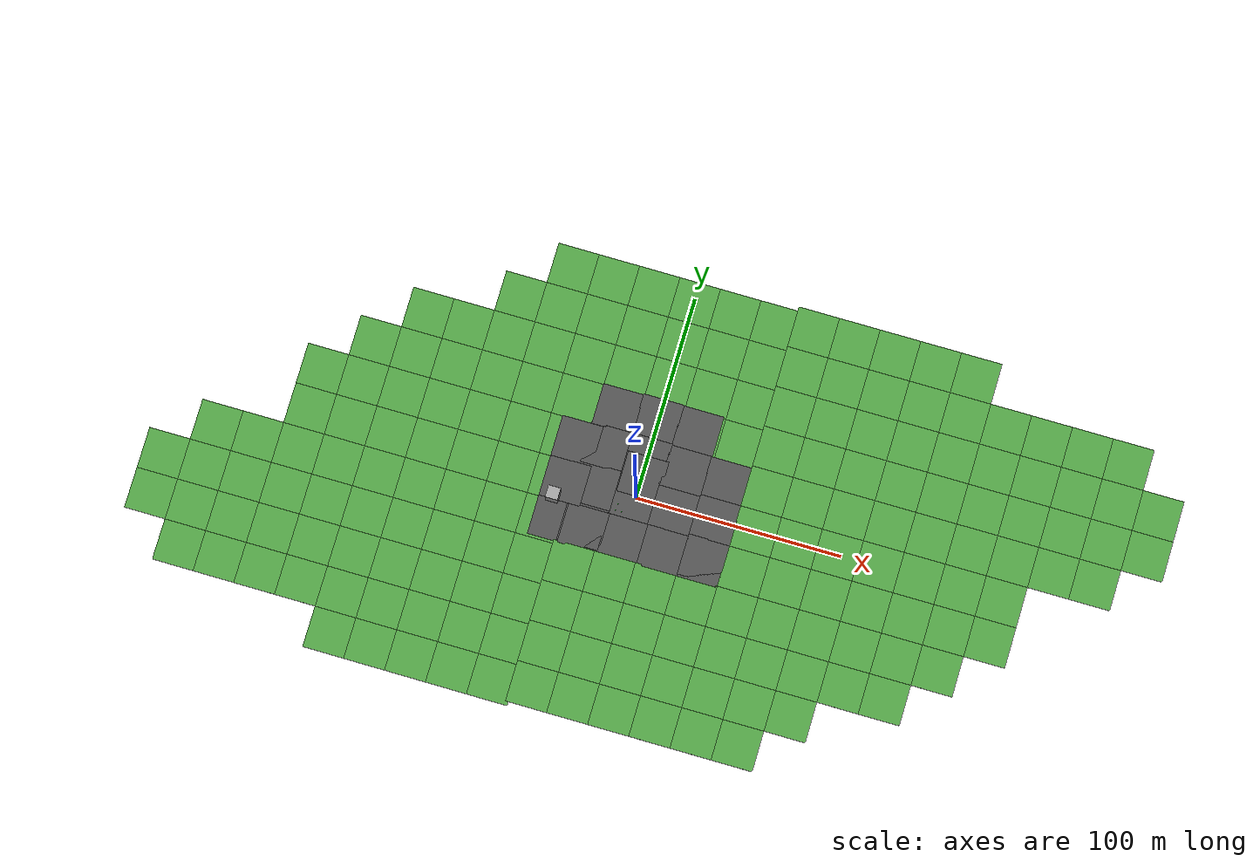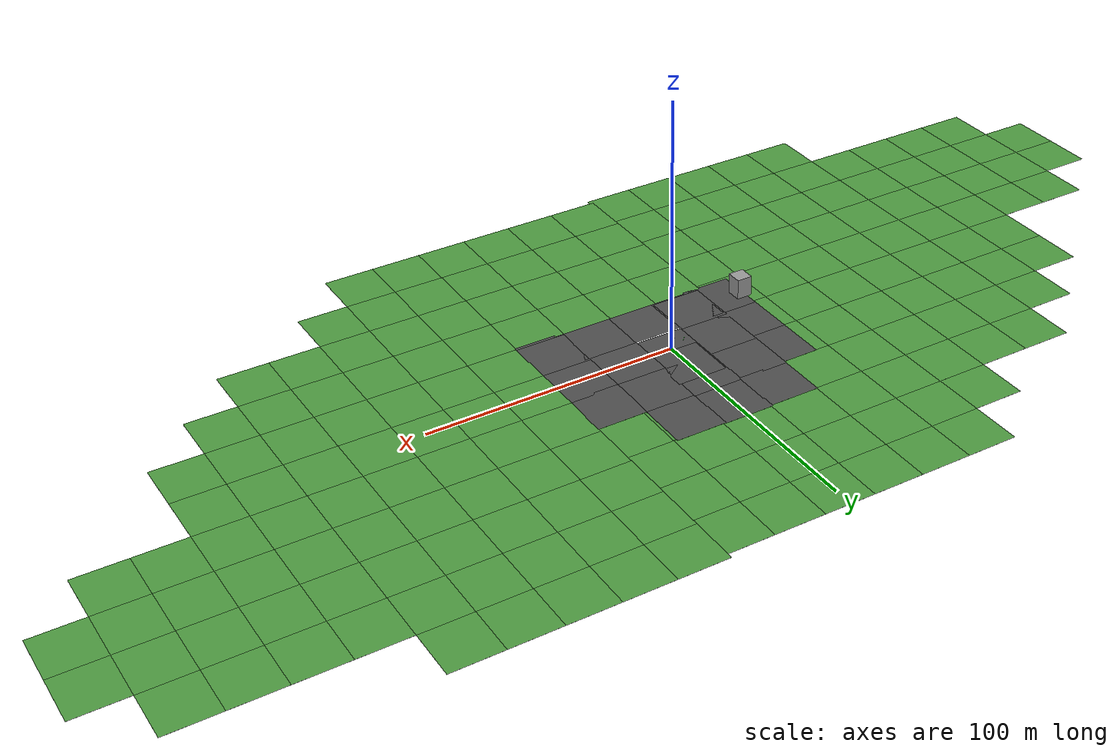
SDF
<sdf version="1.5">
 <world name="default">
  <light name="sun" type="directional">
   <pose>0 0 10 0 -0 0</pose>
   <diffuse>0.8 0.8 0.8 1</diffuse>
   <specular>0.2 0.2 0.2 1</specular>
   <attenuation>
    <range>1000</range>
    <constant>0.9</constant>
    <linear>0.01</linear>
    <quadratic>0.001</quadratic>
   </attenuation>
   <direction>-0.5 0.1 -0.9</direction>
  </light>
  <gravity>0 0 -9.8</gravity>
  <magnetic_field>6e-06 2.3e-05 -4.2e-05</magnetic_field>
  <atmosphere type="adiabatic"/>
  <physics name="default_physics" default="0" type="ode">
   <max_step_size>0.001</max_step_size>
   <real_time_factor>1</real_time_factor>
   <real_time_update_rate>1000</real_time_update_rate>
  </physics>
  <scene><ambient>0.4 0.4 0.4 1</ambient><background>0.7 0.7 0.7 1</background><shadows>1</shadows></scene>
  <spherical_coordinates>
   <surface_model>EARTH_WGS84</surface_model>
   <latitude_deg>0</latitude_deg>
   <longitude_deg>0</longitude_deg>
   <elevation>0</elevation>
   <heading_deg>0</heading_deg>
  </spherical_coordinates>
  <model name="labrob_ground">
   <static>1</static>
   <link name="link">
    <collision name="collision">
     <geometry><plane><normal>0 0 1</normal><size>20 20</size></plane></geometry>
     <surface><friction><ode><mu>100</mu><mu2>50</mu2></ode></friction></surface>
    </collision>
    <visual name="visual">
     <cast_shadows>0</cast_shadows>
     <geometry><plane><normal>0 0 1</normal><size>20 20</size></plane></geometry>
     <material>
      <script>
       <uri>model://labrob_ground/materials/scripts/</uri>
       <uri>model://labrob_ground/materials/textures/</uri>
       <name>Labrob/AsphaltGround</name>
      </script>
     </material>
    </visual>
   </link>
   <pose>-1.13682 -0.729135 0 0 -0 0</pose>
  </model>
  <model name="labrob_ground_0">
   <static>1</static>
   <link name="link">
    <collision name="collision">
     <geometry><plane><normal>0 0 1</normal><size>20 20</size></plane></geometry>
     <surface><friction><ode><mu>100</mu><mu2>50</mu2></ode></friction></surface>
    </collision>
    <visual name="visual">
     <cast_shadows>0</cast_shadows>
     <geometry><plane><normal>0 0 1</normal><size>20 20</size></plane></geometry>
     <material>
      <script>
       <uri>model://labrob_ground/materials/scripts/</uri>
       <uri>model://labrob_ground/materials/textures/</uri>
       <name>Labrob/AsphaltGround</name>
      </script>
     </material>
    </visual>
   </link>
   <pose>18.5231 -0.837953 0 0 -0 0</pose>
  </model>
  <model name="labrob_ground_1">
   <static>1</static>
   <link name="link">
    <collision name="collision">
     <geometry><plane><normal>0 0 1</normal><size>20 20</size></plane></geometry>
     <surface><friction><ode><mu>100</mu><mu2>50</mu2></ode></friction></surface>
    </collision>
    <visual name="visual">
     <cast_shadows>0</cast_shadows>
     <geometry><plane><normal>0 0 1</normal><size>20 20</size></plane></geometry>
     <material>
      <script>
       <uri>model://labrob_ground/materials/scripts/</uri>
       <uri>model://labrob_ground/materials/textures/</uri>
       <name>Labrob/AsphaltGround</name>
      </script>
     </material>
    </visual>
   </link>
   <pose>-1.15349 -20.7136 0 0 -0 0</pose>
  </model>
  <model name="labrob_ground_2">
   <static>1</static>
   <link name="link">
    <collision name="collision">
     <geometry><plane><normal>0 0 1</normal><size>20 20</size></plane></geometry>
     <surface><friction><ode><mu>100</mu><mu2>50</mu2></ode></friction></surface>
    </collision>
    <visual name="visual">
     <cast_shadows>0</cast_shadows>
     <geometry><plane><normal>0 0 1</normal><size>20 20</size></plane></geometry>
     <material>
      <script>
       <uri>model://labrob_ground/materials/scripts/</uri>
       <uri>model://labrob_ground/materials/textures/</uri>
       <name>Labrob/AsphaltGround</name>
      </script>
     </material>
    </visual>
   </link>
   <pose>18.777 -20.6695 0 0 -0 0</pose>
  </model>
  <model name="labrob_ground_3">
   <static>1</static>
   <link name="link">
    <collision name="collision">
     <geometry><plane><normal>0 0 1</normal><size>20 20</size></plane></geometry>
     <surface><friction><ode><mu>100</mu><mu2>50</mu2></ode></friction></surface>
    </collision>
    <visual name="visual">
     <cast_shadows>0</cast_shadows>
     <geometry><plane><normal>0 0 1</normal><size>20 20</size></plane></geometry>
     <material>
      <script>
       <uri>model://labrob_ground/materials/scripts/</uri>
       <uri>model://labrob_ground/materials/textures/</uri>
       <name>Labrob/AsphaltGround</name>
      </script>
     </material>
    </visual>
   </link>
   <pose>-20.4019 0.227461 0 0 -0 0</pose>
  </model>
  <model name="labrob_ground_4">
   <static>1</static>
   <link name="link">
    <collision name="collision">
     <geometry><plane><normal>0 0 1</normal><size>20 20</size></plane></geometry>
     <surface><friction><ode><mu>100</mu><mu2>50</mu2></ode></friction></surface>
    </collision>
    <visual name="visual">
     <cast_shadows>0</cast_shadows>
     <geometry><plane><normal>0 0 1</normal><size>20 20</size></plane></geometry>
     <material>
      <script>
       <uri>model://labrob_ground/materials/scripts/</uri>
       <uri>model://labrob_ground/materials/textures/</uri>
       <name>Labrob/AsphaltGround</name>
      </script>
     </material>
    </visual>
   </link>
   <pose>-20.6052 -19.5078 0 0 -0 0</pose>
  </model>
  <model name="labrob_ground_5">
   <static>1</static>
   <link name="link">
    <collision name="collision">
     <geometry><plane><normal>0 0 1</normal><size>20 20</size></plane></geometry>
     <surface><friction><ode><mu>100</mu><mu2>50</mu2></ode></friction></surface>
    </collision>
    <visual name="visual">
     <cast_shadows>0</cast_shadows>
     <geometry><plane><normal>0 0 1</normal><size>20 20</size></plane></geometry>
     <material>
      <script>
       <uri>model://labrob_ground/materials/scripts/</uri>
       <uri>model://labrob_ground/materials/textures/</uri>
       <name>Labrob/AsphaltGround</name>
      </script>
     </material>
    </visual>
   </link>
   <pose>-20.4308 19.4095 0 0 -0 0</pose>
  </model>
  <model name="labrob_ground_6">
   <static>1</static>
   <link name="link">
    <collision name="collision">
     <geometry><plane><normal>0 0 1</normal><size>20 20</size></plane></geometry>
     <surface><friction><ode><mu>100</mu><mu2>50</mu2></ode></friction></surface>
    </collision>
    <visual name="visual">
     <cast_shadows>0</cast_shadows>
     <geometry><plane><normal>0 0 1</normal><size>20 20</size></plane></geometry>
     <material>
      <script>
       <uri>model://labrob_ground/materials/scripts/</uri>
       <uri>model://labrob_ground/materials/textures/</uri>
       <name>Labrob/AsphaltGround</name>
      </script>
     </material>
    </visual>
   </link>
   <pose>-0.764551 19.5561 0 0 -0 0</pose>
  </model>
  <model name="labrob_ground_7">
   <static>1</static>
   <link name="link">
    <collision name="collision">
     <geometry><plane><normal>0 0 1</normal><size>20 20</size></plane></geometry>
     <surface><friction><ode><mu>100</mu><mu2>50</mu2></ode></friction></surface>
    </collision>
    <visual name="visual">
     <cast_shadows>0</cast_shadows>
     <geometry><plane><normal>0 0 1</normal><size>20 20</size></plane></geometry>
     <material>
      <script>
       <uri>model://labrob_ground/materials/scripts/</uri>
       <uri>model://labrob_ground/materials/textures/</uri>
       <name>Labrob/AsphaltGround</name>
      </script>
     </material>
    </visual>
   </link>
   <pose>18.7361 18.9694 0 0 -0 0</pose>
  </model>
  <model name="labrob_ground_8">
   <static>1</static>
   <link name="link">
    <collision name="collision">
     <geometry><plane><normal>0 0 1</normal><size>20 20</size></plane></geometry>
     <surface><friction><ode><mu>100</mu><mu2>50</mu2></ode></friction></surface>
    </collision>
    <visual name="visual">
     <cast_shadows>0</cast_shadows>
     <geometry><plane><normal>0 0 1</normal><size>20 20</size></plane></geometry>
     <material>
      <script>
       <uri>model://labrob_ground/materials/scripts/</uri>
       <uri>model://labrob_ground/materials/textures/</uri>
       <name>Labrob/AsphaltGround</name>
      </script>
     </material>
    </visual>
   </link>
   <pose>-20.2712 38.534 0 0 -0 0</pose>
  </model>
  <model name="labrob_ground_9">
   <static>1</static>
   <link name="link">
    <collision name="collision">
     <geometry><plane><normal>0 0 1</normal><size>20 20</size></plane></geometry>
     <surface><friction><ode><mu>100</mu><mu2>50</mu2></ode></friction></surface>
    </collision>
    <visual name="visual">
     <cast_shadows>0</cast_shadows>
     <geometry><plane><normal>0 0 1</normal><size>20 20</size></plane></geometry>
     <material>
      <script>
       <uri>model://labrob_ground/materials/scripts/</uri>
       <uri>model://labrob_ground/materials/textures/</uri>
       <name>Labrob/AsphaltGround</name>
      </script>
     </material>
    </visual>
   </link>
   <pose>-0.706199 39.0779 0 0 -0 0</pose>
  </model>
  <model name="labrob_ground_10">
   <static>1</static>
   <link name="link">
    <collision name="collision">
     <geometry><plane><normal>0 0 1</normal><size>20 20</size></plane></geometry>
     <surface><friction><ode><mu>100</mu><mu2>50</mu2></ode></friction></surface>
    </collision>
    <visual name="visual">
     <cast_shadows>0</cast_shadows>
     <geometry><plane><normal>0 0 1</normal><size>20 20</size></plane></geometry>
     <material>
      <script>
       <uri>model://labrob_ground/materials/scripts/</uri>
       <uri>model://labrob_ground/materials/textures/</uri>
       <name>Labrob/AsphaltGround</name>
      </script>
     </material>
    </visual>
   </link>
   <pose>18.9313 38.763 0 0 -0 0</pose>
  </model>
  <model name="labrob_ground_11">
   <static>1</static>
   <link name="link">
    <collision name="collision">
     <geometry><plane><normal>0 0 1</normal><size>20 20</size></plane></geometry>
     <surface><friction><ode><mu>100</mu><mu2>50</mu2></ode></friction></surface>
    </collision>
    <visual name="visual">
     <cast_shadows>0</cast_shadows>
     <geometry><plane><normal>0 0 1</normal><size>20 20</size></plane></geometry>
     <material>
      <script>
       <uri>model://labrob_ground/materials/scripts/</uri>
       <uri>model://labrob_ground/materials/textures/</uri>
       <name>Labrob/AsphaltGround</name>
      </script>
     </material>
    </visual>
   </link>
   <pose>38.4891 18.8271 0 0 -0 0</pose>
  </model>
  <model name="labrob_ground_12">
   <static>1</static>
   <link name="link">
    <collision name="collision">
     <geometry><plane><normal>0 0 1</normal><size>20 20</size></plane></geometry>
     <surface><friction><ode><mu>100</mu><mu2>50</mu2></ode></friction></surface>
    </collision>
    <visual name="visual">
     <cast_shadows>0</cast_shadows>
     <geometry><plane><normal>0 0 1</normal><size>20 20</size></plane></geometry>
     <material>
      <script>
       <uri>model://labrob_ground/materials/scripts/</uri>
       <uri>model://labrob_ground/materials/textures/</uri>
       <name>Labrob/AsphaltGround</name>
      </script>
     </material>
    </visual>
   </link>
   <pose>38.5118 0.043136 0 0 -0 0</pose>
  </model>
  <model name="labrob_ground_13">
   <static>1</static>
   <link name="link">
    <collision name="collision">
     <geometry><plane><normal>0 0 1</normal><size>20 20</size></plane></geometry>
     <surface><friction><ode><mu>100</mu><mu2>50</mu2></ode></friction></surface>
    </collision>
    <visual name="visual">
     <cast_shadows>0</cast_shadows>
     <geometry><plane><normal>0 0 1</normal><size>20 20</size></plane></geometry>
     <material>
      <script>
       <uri>model://labrob_ground/materials/scripts/</uri>
       <uri>model://labrob_ground/materials/textures/</uri>
       <name>Labrob/AsphaltGround</name>
      </script>
     </material>
    </visual>
   </link>
   <pose>38.4883 -19.6209 0 0 -0 0</pose>
  </model>
  <model name="labrob_ground_14">
   <static>1</static>
   <link name="link">
    <collision name="collision">
     <geometry><plane><normal>0 0 1</normal><size>20 20</size></plane></geometry>
     <surface><friction><ode><mu>100</mu><mu2>50</mu2></ode></friction></surface>
    </collision>
    <visual name="visual">
     <cast_shadows>0</cast_shadows>
     <geometry><plane><normal>0 0 1</normal><size>20 20</size></plane></geometry>
     <material>
      <script>
       <uri>model://labrob_ground/materials/scripts/</uri>
       <uri>model://labrob_ground/materials/textures/</uri>
       <name>Labrob/AsphaltGround</name>
      </script>
     </material>
    </visual>
   </link>
   <pose>-19.9414 -20.7737 0 0 -0 0</pose>
  </model>
  <model name="labrob_ground_15">
   <static>1</static>
   <link name="link">
    <collision name="collision">
     <geometry><plane><normal>0 0 1</normal><size>20 20</size></plane></geometry>
     <surface><friction><ode><mu>100</mu><mu2>50</mu2></ode></friction></surface>
    </collision>
    <visual name="visual">
     <cast_shadows>0</cast_shadows>
     <geometry><plane><normal>0 0 1</normal><size>20 20</size></plane></geometry>
     <material>
      <script>
       <uri>model://labrob_ground/materials/scripts/</uri>
       <uri>model://labrob_ground/materials/textures/</uri>
       <name>Labrob/AsphaltGround</name>
      </script>
     </material>
    </visual>
   </link>
   <pose>-34.5431 -20.6915 0 0 -0 0</pose>
  </model>
  <model name="labrob_ground_16">
   <static>1</static>
   <link name="link">
    <collision name="collision">
     <geometry><plane><normal>0 0 1</normal><size>20 20</size></plane></geometry>
     <surface><friction><ode><mu>100</mu><mu2>50</mu2></ode></friction></surface>
    </collision>
    <visual name="visual">
     <cast_shadows>0</cast_shadows>
     <geometry><plane><normal>0 0 1</normal><size>20 20</size></plane></geometry>
     <material>
      <script>
       <uri>model://labrob_ground/materials/scripts/</uri>
       <uri>model://labrob_ground/materials/textures/</uri>
       <name>Labrob/AsphaltGround</name>
      </script>
     </material>
    </visual>
   </link>
   <pose>-34.5552 -1.44397 0 0 -0 0</pose>
  </model>
  <model name="labrob_ground_17">
   <static>1</static>
   <link name="link">
    <collision name="collision">
     <geometry><plane><normal>0 0 1</normal><size>20 20</size></plane></geometry>
     <surface><friction><ode><mu>100</mu><mu2>50</mu2></ode></friction></surface>
    </collision>
    <visual name="visual">
     <cast_shadows>0</cast_shadows>
     <geometry><plane><normal>0 0 1</normal><size>20 20</size></plane></geometry>
     <material>
      <script>
       <uri>model://labrob_ground/materials/scripts/</uri>
       <uri>model://labrob_ground/materials/textures/</uri>
       <name>Labrob/AsphaltGround</name>
      </script>
     </material>
    </visual>
   </link>
   <pose>-34.5316 18.4059 0 0 -0 0</pose>
  </model>
  <model name="labrob_ground_18">
   <static>1</static>
   <link name="link">
    <collision name="collision">
     <geometry><plane><normal>0 0 1</normal><size>20 20</size></plane></geometry>
     <surface><friction><ode><mu>100</mu><mu2>50</mu2></ode></friction></surface>
    </collision>
    <visual name="visual">
     <cast_shadows>0</cast_shadows>
     <geometry><plane><normal>0 0 1</normal><size>20 20</size></plane></geometry>
     <material>
      <script>
       <uri>model://labrob_ground/materials/scripts/</uri>
       <uri>model://labrob_ground/materials/textures/</uri>
       <name>Labrob/AsphaltGround</name>
      </script>
     </material>
    </visual>
   </link>
   <pose>38.422 -20.7287 0 0 -0 0</pose>
  </model>
  <model name="grass_plane">
   <static>1</static>
   <link name="link">
    <collision name="collision">
     <geometry><plane><normal>0 0 1</normal><size>500 500</size></plane></geometry>
     <surface><friction><ode><mu>0.5</mu><mu2>0.5</mu2></ode></friction></surface>
    </collision>
    <visual name="visual_0">
     <pose>-40 -40 0 0 -0 0</pose>
     <cast_shadows>0</cast_shadows>
     <geometry><plane><normal>0 0 1</normal><size>20 20</size></plane></geometry>
     <material>
      <script>
       <uri>model://grass_plane/materials/scripts</uri>
       <uri>model://grass_plane/materials/textures</uri>
       <name>vrc/grass</name>
      </script>
     </material>
    </visual>
    <visual name="visual_1">
     <pose>-20 -40 0 0 -0 0</pose>
     <cast_shadows>0</cast_shadows>
     <geometry><plane><normal>0 0 1</normal><size>20 20</size></plane></geometry>
     <material>
      <script>
       <uri>model://grass_plane/materials/scripts</uri>
       <uri>model://grass_plane/materials/textures</uri>
       <name>vrc/grass</name>
      </script>
     </material>
    </visual>
    <visual name="visual_2">
     <pose>0 -40 0 0 -0 0</pose>
     <cast_shadows>0</cast_shadows>
     <geometry><plane><normal>0 0 1</normal><size>20 20</size></plane></geometry>
     <material>
      <script>
       <uri>model://grass_plane/materials/scripts</uri>
       <uri>model://grass_plane/materials/textures</uri>
       <name>vrc/grass</name>
      </script>
     </material>
    </visual>
    <visual name="visual_3">
     <pose>20 -40 0 0 -0 0</pose>
     <cast_shadows>0</cast_shadows>
     <geometry><plane><normal>0 0 1</normal><size>20 20</size></plane></geometry>
     <material>
      <script>
       <uri>model://grass_plane/materials/scripts</uri>
       <uri>model://grass_plane/materials/textures</uri>
       <name>vrc/grass</name>
      </script>
     </material>
    </visual>
    <visual name="visual_4">
     <pose>40 -40 0 0 -0 0</pose>
     <cast_shadows>0</cast_shadows>
     <geometry><plane><normal>0 0 1</normal><size>20 20</size></plane></geometry>
     <material>
      <script>
       <uri>model://grass_plane/materials/scripts</uri>
       <uri>model://grass_plane/materials/textures</uri>
       <name>vrc/grass</name>
      </script>
     </material>
    </visual>
    <visual name="visual_5">
     <pose>60 -40 0 0 -0 0</pose>
     <cast_shadows>0</cast_shadows>
     <geometry><plane><normal>0 0 1</normal><size>20 20</size></plane></geometry>
     <material>
      <script>
       <uri>model://grass_plane/materials/scripts</uri>
       <uri>model://grass_plane/materials/textures</uri>
       <name>vrc/grass</name>
      </script>
     </material>
    </visual>
    <visual name="visual_6">
     <pose>-40 -20 0 0 -0 0</pose>
     <cast_shadows>0</cast_shadows>
     <geometry><plane><normal>0 0 1</normal><size>20 20</size></plane></geometry>
     <material>
      <script>
       <uri>model://grass_plane/materials/scripts</uri>
       <uri>model://grass_plane/materials/textures</uri>
       <name>vrc/grass</name>
      </script>
     </material>
    </visual>
    <visual name="visual_7">
     <pose>-20 -20 0 0 -0 0</pose>
     <cast_shadows>0</cast_shadows>
     <geometry><plane><normal>0 0 1</normal><size>20 20</size></plane></geometry>
     <material>
      <script>
       <uri>model://grass_plane/materials/scripts</uri>
       <uri>model://grass_plane/materials/textures</uri>
       <name>vrc/grass</name>
      </script>
     </material>
    </visual>
    <visual name="visual_8">
     <pose>0 -20 0 0 -0 0</pose>
     <cast_shadows>0</cast_shadows>
     <geometry><plane><normal>0 0 1</normal><size>20 20</size></plane></geometry>
     <material>
      <script>
       <uri>model://grass_plane/materials/scripts</uri>
       <uri>model://grass_plane/materials/textures</uri>
       <name>vrc/grass</name>
      </script>
     </material>
    </visual>
    <visual name="visual_9">
     <pose>20 -20 0 0 -0 0</pose>
     <cast_shadows>0</cast_shadows>
     <geometry><plane><normal>0 0 1</normal><size>20 20</size></plane></geometry>
     <material>
      <script>
       <uri>model://grass_plane/materials/scripts</uri>
       <uri>model://grass_plane/materials/textures</uri>
       <name>vrc/grass</name>
      </script>
     </material>
    </visual>
    <visual name="visual_10">
     <pose>40 -20 0 0 -0 0</pose>
     <cast_shadows>0</cast_shadows>
     <geometry><plane><normal>0 0 1</normal><size>20 20</size></plane></geometry>
     <material>
      <script>
       <uri>model://grass_plane/materials/scripts</uri>
       <uri>model://grass_plane/materials/textures</uri>
       <name>vrc/grass</name>
      </script>
     </material>
    </visual>
    <visual name="visual_11">
     <pose>60 -20 0 0 -0 0</pose>
     <cast_shadows>0</cast_shadows>
     <geometry><plane><normal>0 0 1</normal><size>20 20</size></plane></geometry>
     <material>
      <script>
       <uri>model://grass_plane/materials/scripts</uri>
       <uri>model://grass_plane/materials/textures</uri>
       <name>vrc/grass</name>
      </script>
     </material>
    </visual>
    <visual name="visual_12">
     <pose>80 -20 0 0 -0 0</pose>
     <cast_shadows>0</cast_shadows>
     <geometry><plane><normal>0 0 1</normal><size>20 20</size></plane></geometry>
     <material>
      <script>
       <uri>model://grass_plane/materials/scripts</uri>
       <uri>model://grass_plane/materials/textures</uri>
       <name>vrc/grass</name>
      </script>
     </material>
    </visual>
    <visual name="visual_13">
     <pose>-40 0 0 0 -0 0</pose>
     <cast_shadows>0</cast_shadows>
     <geometry><plane><normal>0 0 1</normal><size>20 20</size></plane></geometry>
     <material>
      <script>
       <uri>model://grass_plane/materials/scripts</uri>
       <uri>model://grass_plane/materials/textures</uri>
       <name>vrc/grass</name>
      </script>
     </material>
    </visual>
    <visual name="visual_14">
     <pose>-20 0 0 0 -0 0</pose>
     <cast_shadows>0</cast_shadows>
     <geometry><plane><normal>0 0 1</normal><size>20 20</size></plane></geometry>
     <material>
      <script>
       <uri>model://grass_plane/materials/scripts</uri>
       <uri>model://grass_plane/materials/textures</uri>
       <name>vrc/grass</name>
      </script>
     </material>
    </visual>
    <visual name="visual_15">
     <cast_shadows>0</cast_shadows>
     <geometry><plane><normal>0 0 1</normal><size>20 20</size></plane></geometry>
     <material>
      <script>
       <uri>model://grass_plane/materials/scripts</uri>
       <uri>model://grass_plane/materials/textures</uri>
       <name>vrc/grass</name>
      </script>
     </material>
    </visual>
    <visual name="visual_16">
     <pose>20 0 0 0 -0 0</pose>
     <cast_shadows>0</cast_shadows>
     <geometry><plane><normal>0 0 1</normal><size>20 20</size></plane></geometry>
     <material>
      <script>
       <uri>model://grass_plane/materials/scripts</uri>
       <uri>model://grass_plane/materials/textures</uri>
       <name>vrc/grass</name>
      </script>
     </material>
    </visual>
    <visual name="visual_17">
     <pose>40 0 0 0 -0 0</pose>
     <cast_shadows>0</cast_shadows>
     <geometry><plane><normal>0 0 1</normal><size>20 20</size></plane></geometry>
     <material>
      <script>
       <uri>model://grass_plane/materials/scripts</uri>
       <uri>model://grass_plane/materials/textures</uri>
       <name>vrc/grass</name>
      </script>
     </material>
    </visual>
    <visual name="visual_18">
     <pose>60 0 0 0 -0 0</pose>
     <cast_shadows>0</cast_shadows>
     <geometry><plane><normal>0 0 1</normal><size>20 20</size></plane></geometry>
     <material>
      <script>
       <uri>model://grass_plane/materials/scripts</uri>
       <uri>model://grass_plane/materials/textures</uri>
       <name>vrc/grass</name>
      </script>
     </material>
    </visual>
    <visual name="visual_19">
     <pose>80 0 0 0 -0 0</pose>
     <cast_shadows>0</cast_shadows>
     <geometry><plane><normal>0 0 1</normal><size>20 20</size></plane></geometry>
     <material>
      <script>
       <uri>model://grass_plane/materials/scripts</uri>
       <uri>model://grass_plane/materials/textures</uri>
       <name>vrc/grass</name>
      </script>
     </material>
    </visual>
    <visual name="visual_20">
     <pose>100 0 0 0 -0 0</pose>
     <cast_shadows>0</cast_shadows>
     <geometry><plane><normal>0 0 1</normal><size>20 20</size></plane></geometry>
     <material>
      <script>
       <uri>model://grass_plane/materials/scripts</uri>
       <uri>model://grass_plane/materials/textures</uri>
       <name>vrc/grass</name>
      </script>
     </material>
    </visual>
    <visual name="visual_21">
     <pose>120 0 0 0 -0 0</pose>
     <cast_shadows>0</cast_shadows>
     <geometry><plane><normal>0 0 1</normal><size>20 20</size></plane></geometry>
     <material>
      <script>
       <uri>model://grass_plane/materials/scripts</uri>
       <uri>model://grass_plane/materials/textures</uri>
       <name>vrc/grass</name>
      </script>
     </material>
    </visual>
    <visual name="visual_22">
     <pose>-40 20 0 0 -0 0</pose>
     <cast_shadows>0</cast_shadows>
     <geometry><plane><normal>0 0 1</normal><size>20 20</size></plane></geometry>
     <material>
      <script>
       <uri>model://grass_plane/materials/scripts</uri>
       <uri>model://grass_plane/materials/textures</uri>
       <name>vrc/grass</name>
      </script>
     </material>
    </visual>
    <visual name="visual_23">
     <pose>-20 20 0 0 -0 0</pose>
     <cast_shadows>0</cast_shadows>
     <geometry><plane><normal>0 0 1</normal><size>20 20</size></plane></geometry>
     <material>
      <script>
       <uri>model://grass_plane/materials/scripts</uri>
       <uri>model://grass_plane/materials/textures</uri>
       <name>vrc/grass</name>
      </script>
     </material>
    </visual>
    <visual name="visual_24">
     <pose>0 20 0 0 -0 0</pose>
     <cast_shadows>0</cast_shadows>
     <geometry><plane><normal>0 0 1</normal><size>20 20</size></plane></geometry>
     <material>
      <script>
       <uri>model://grass_plane/materials/scripts</uri>
       <uri>model://grass_plane/materials/textures</uri>
       <name>vrc/grass</name>
      </script>
     </material>
    </visual>
    <visual name="visual_25">
     <pose>20 20 0 0 -0 0</pose>
     <cast_shadows>0</cast_shadows>
     <geometry><plane><normal>0 0 1</normal><size>20 20</size></plane></geometry>
     <material>
      <script>
       <uri>model://grass_plane/materials/scripts</uri>
       <uri>model://grass_plane/materials/textures</uri>
       <name>vrc/grass</name>
      </script>
     </material>
    </visual>
    <visual name="visual_26">
     <pose>40 20 0 0 -0 0</pose>
     <cast_shadows>0</cast_shadows>
     <geometry><plane><normal>0 0 1</normal><size>20 20</size></plane></geometry>
     <material>
      <script>
       <uri>model://grass_plane/materials/scripts</uri>
       <uri>model://grass_plane/materials/textures</uri>
       <name>vrc/grass</name>
      </script>
     </material>
    </visual>
    <visual name="visual_27">
     <pose>60 20 0 0 -0 0</pose>
     <cast_shadows>0</cast_shadows>
     <geometry><plane><normal>0 0 1</normal><size>20 20</size></plane></geometry>
     <material>
      <script>
       <uri>model://grass_plane/materials/scripts</uri>
       <uri>model://grass_plane/materials/textures</uri>
       <name>vrc/grass</name>
      </script>
     </material>
    </visual>
    <visual name="visual_28">
     <pose>80 20 0 0 -0 0</pose>
     <cast_shadows>0</cast_shadows>
     <geometry><plane><normal>0 0 1</normal><size>20 20</size></plane></geometry>
     <material>
      <script>
       <uri>model://grass_plane/materials/scripts</uri>
       <uri>model://grass_plane/materials/textures</uri>
       <name>vrc/grass</name>
      </script>
     </material>
    </visual>
    <visual name="visual_29">
     <pose>100 20 0 0 -0 0</pose>
     <cast_shadows>0</cast_shadows>
     <geometry><plane><normal>0 0 1</normal><size>20 20</size></plane></geometry>
     <material>
      <script>
       <uri>model://grass_plane/materials/scripts</uri>
       <uri>model://grass_plane/materials/textures</uri>
       <name>vrc/grass</name>
      </script>
     </material>
    </visual>
    <visual name="visual_30">
     <pose>120 20 0 0 -0 0</pose>
     <cast_shadows>0</cast_shadows>
     <geometry><plane><normal>0 0 1</normal><size>20 20</size></plane></geometry>
     <material>
      <script>
       <uri>model://grass_plane/materials/scripts</uri>
       <uri>model://grass_plane/materials/textures</uri>
       <name>vrc/grass</name>
      </script>
     </material>
    </visual>
    <visual name="visual_31">
     <pose>140 20 0 0 -0 0</pose>
     <cast_shadows>0</cast_shadows>
     <geometry><plane><normal>0 0 1</normal><size>20 20</size></plane></geometry>
     <material>
      <script>
       <uri>model://grass_plane/materials/scripts</uri>
       <uri>model://grass_plane/materials/textures</uri>
       <name>vrc/grass</name>
      </script>
     </material>
    </visual>
    <visual name="visual_32">
     <pose>40 40 0 0 -0 0</pose>
     <cast_shadows>0</cast_shadows>
     <geometry><plane><normal>0 0 1</normal><size>20 20</size></plane></geometry>
     <material>
      <script>
       <uri>model://grass_plane/materials/scripts</uri>
       <uri>model://grass_plane/materials/textures</uri>
       <name>vrc/grass</name>
      </script>
     </material>
    </visual>
    <visual name="visual_33">
     <pose>60 40 0 0 -0 0</pose>
     <cast_shadows>0</cast_shadows>
     <geometry><plane><normal>0 0 1</normal><size>20 20</size></plane></geometry>
     <material>
      <script>
       <uri>model://grass_plane/materials/scripts</uri>
       <uri>model://grass_plane/materials/textures</uri>
       <name>vrc/grass</name>
      </script>
     </material>
    </visual>
    <visual name="visual_34">
     <pose>80 40 0 0 -0 0</pose>
     <cast_shadows>0</cast_shadows>
     <geometry><plane><normal>0 0 1</normal><size>20 20</size></plane></geometry>
     <material>
      <script>
       <uri>model://grass_plane/materials/scripts</uri>
       <uri>model://grass_plane/materials/textures</uri>
       <name>vrc/grass</name>
      </script>
     </material>
    </visual>
    <visual name="visual_35">
     <pose>100 40 0 0 -0 0</pose>
     <cast_shadows>0</cast_shadows>
     <geometry><plane><normal>0 0 1</normal><size>20 20</size></plane></geometry>
     <material>
      <script>
       <uri>model://grass_plane/materials/scripts</uri>
       <uri>model://grass_plane/materials/textures</uri>
       <name>vrc/grass</name>
      </script>
     </material>
    </visual>
    <visual name="visual_36">
     <pose>120 40 0 0 -0 0</pose>
     <cast_shadows>0</cast_shadows>
     <geometry><plane><normal>0 0 1</normal><size>20 20</size></plane></geometry>
     <material>
      <script>
       <uri>model://grass_plane/materials/scripts</uri>
       <uri>model://grass_plane/materials/textures</uri>
       <name>vrc/grass</name>
      </script>
     </material>
    </visual>
    <visual name="visual_37">
     <pose>140 40 0 0 -0 0</pose>
     <cast_shadows>0</cast_shadows>
     <geometry><plane><normal>0 0 1</normal><size>20 20</size></plane></geometry>
     <material>
      <script>
       <uri>model://grass_plane/materials/scripts</uri>
       <uri>model://grass_plane/materials/textures</uri>
       <name>vrc/grass</name>
      </script>
     </material>
    </visual>
    <visual name="visual_38">
     <pose>160 40 0 0 -0 0</pose>
     <cast_shadows>0</cast_shadows>
     <geometry><plane><normal>0 0 1</normal><size>20 20</size></plane></geometry>
     <material>
      <script>
       <uri>model://grass_plane/materials/scripts</uri>
       <uri>model://grass_plane/materials/textures</uri>
       <name>vrc/grass</name>
      </script>
     </material>
    </visual>
    <visual name="visual_39">
     <pose>40 60 0 0 -0 0</pose>
     <cast_shadows>0</cast_shadows>
     <geometry><plane><normal>0 0 1</normal><size>20 20</size></plane></geometry>
     <material>
      <script>
       <uri>model://grass_plane/materials/scripts</uri>
       <uri>model://grass_plane/materials/textures</uri>
       <name>vrc/grass</name>
      </script>
     </material>
    </visual>
    <visual name="visual_40">
     <pose>60 60 0 0 -0 0</pose>
     <cast_shadows>0</cast_shadows>
     <geometry><plane><normal>0 0 1</normal><size>20 20</size></plane></geometry>
     <material>
      <script>
       <uri>model://grass_plane/materials/scripts</uri>
       <uri>model://grass_plane/materials/textures</uri>
       <name>vrc/grass</name>
      </script>
     </material>
    </visual>
    <visual name="visual_41">
     <pose>80 60 0 0 -0 0</pose>
     <cast_shadows>0</cast_shadows>
     <geometry><plane><normal>0 0 1</normal><size>20 20</size></plane></geometry>
     <material>
      <script>
       <uri>model://grass_plane/materials/scripts</uri>
       <uri>model://grass_plane/materials/textures</uri>
       <name>vrc/grass</name>
      </script>
     </material>
    </visual>
    <visual name="visual_42">
     <pose>100 60 0 0 -0 0</pose>
     <cast_shadows>0</cast_shadows>
     <geometry><plane><normal>0 0 1</normal><size>20 20</size></plane></geometry>
     <material>
      <script>
       <uri>model://grass_plane/materials/scripts</uri>
       <uri>model://grass_plane/materials/textures</uri>
       <name>vrc/grass</name>
      </script>
     </material>
    </visual>
    <visual name="visual_43">
     <pose>120 60 0 0 -0 0</pose>
     <cast_shadows>0</cast_shadows>
     <geometry><plane><normal>0 0 1</normal><size>20 20</size></plane></geometry>
     <material>
      <script>
       <uri>model://grass_plane/materials/scripts</uri>
       <uri>model://grass_plane/materials/textures</uri>
       <name>vrc/grass</name>
      </script>
     </material>
    </visual>
    <visual name="visual_44">
     <pose>140 60 0 0 -0 0</pose>
     <cast_shadows>0</cast_shadows>
     <geometry><plane><normal>0 0 1</normal><size>20 20</size></plane></geometry>
     <material>
      <script>
       <uri>model://grass_plane/materials/scripts</uri>
       <uri>model://grass_plane/materials/textures</uri>
       <name>vrc/grass</name>
      </script>
     </material>
    </visual>
    <visual name="visual_45">
     <pose>160 60 0 0 -0 0</pose>
     <cast_shadows>0</cast_shadows>
     <geometry><plane><normal>0 0 1</normal><size>20 20</size></plane></geometry>
     <material>
      <script>
       <uri>model://grass_plane/materials/scripts</uri>
       <uri>model://grass_plane/materials/textures</uri>
       <name>vrc/grass</name>
      </script>
     </material>
    </visual>
    <visual name="visual_46">
     <pose>40 80 0 0 -0 0</pose>
     <cast_shadows>0</cast_shadows>
     <geometry><plane><normal>0 0 1</normal><size>20 20</size></plane></geometry>
     <material>
      <script>
       <uri>model://grass_plane/materials/scripts</uri>
       <uri>model://grass_plane/materials/textures</uri>
       <name>vrc/grass</name>
      </script>
     </material>
    </visual>
    <visual name="visual_47">
     <pose>60 80 0 0 -0 0</pose>
     <cast_shadows>0</cast_shadows>
     <geometry><plane><normal>0 0 1</normal><size>20 20</size></plane></geometry>
     <material>
      <script>
       <uri>model://grass_plane/materials/scripts</uri>
       <uri>model://grass_plane/materials/textures</uri>
       <name>vrc/grass</name>
      </script>
     </material>
    </visual>
    <visual name="visual_48">
     <pose>80 80 0 0 -0 0</pose>
     <cast_shadows>0</cast_shadows>
     <geometry><plane><normal>0 0 1</normal><size>20 20</size></plane></geometry>
     <material>
      <script>
       <uri>model://grass_plane/materials/scripts</uri>
       <uri>model://grass_plane/materials/textures</uri>
       <name>vrc/grass</name>
      </script>
     </material>
    </visual>
    <visual name="visual_49">
     <pose>100 80 0 0 -0 0</pose>
     <cast_shadows>0</cast_shadows>
     <geometry><plane><normal>0 0 1</normal><size>20 20</size></plane></geometry>
     <material>
      <script>
       <uri>model://grass_plane/materials/scripts</uri>
       <uri>model://grass_plane/materials/textures</uri>
       <name>vrc/grass</name>
      </script>
     </material>
    </visual>
    <visual name="visual_50">
     <pose>120 80 0 0 -0 0</pose>
     <cast_shadows>0</cast_shadows>
     <geometry><plane><normal>0 0 1</normal><size>20 20</size></plane></geometry>
     <material>
      <script>
       <uri>model://grass_plane/materials/scripts</uri>
       <uri>model://grass_plane/materials/textures</uri>
       <name>vrc/grass</name>
      </script>
     </material>
    </visual>
    <visual name="visual_51">
     <pose>140 80 0 0 -0 0</pose>
     <cast_shadows>0</cast_shadows>
     <geometry><plane><normal>0 0 1</normal><size>20 20</size></plane></geometry>
     <material>
      <script>
       <uri>model://grass_plane/materials/scripts</uri>
       <uri>model://grass_plane/materials/textures</uri>
       <name>vrc/grass</name>
      </script>
     </material>
    </visual>
    <visual name="visual_52">
     <pose>160 80 0 0 -0 0</pose>
     <cast_shadows>0</cast_shadows>
     <geometry><plane><normal>0 0 1</normal><size>20 20</size></plane></geometry>
     <material>
      <script>
       <uri>model://grass_plane/materials/scripts</uri>
       <uri>model://grass_plane/materials/textures</uri>
       <name>vrc/grass</name>
      </script>
     </material>
    </visual>
    <visual name="visual_53">
     <pose>180 80 0 0 -0 0</pose>
     <cast_shadows>0</cast_shadows>
     <geometry><plane><normal>0 0 1</normal><size>20 20</size></plane></geometry>
     <material>
      <script>
       <uri>model://grass_plane/materials/scripts</uri>
       <uri>model://grass_plane/materials/textures</uri>
       <name>vrc/grass</name>
      </script>
     </material>
    </visual>
    <visual name="visual_54">
     <pose>200 80 0 0 -0 0</pose>
     <cast_shadows>0</cast_shadows>
     <geometry><plane><normal>0 0 1</normal><size>20 20</size></plane></geometry>
     <material>
      <script>
       <uri>model://grass_plane/materials/scripts</uri>
       <uri>model://grass_plane/materials/textures</uri>
       <name>vrc/grass</name>
      </script>
     </material>
    </visual>
    <visual name="visual_55">
     <pose>40 100 0 0 -0 0</pose>
     <cast_shadows>0</cast_shadows>
     <geometry><plane><normal>0 0 1</normal><size>20 20</size></plane></geometry>
     <material>
      <script>
       <uri>model://grass_plane/materials/scripts</uri>
       <uri>model://grass_plane/materials/textures</uri>
       <name>vrc/grass</name>
      </script>
     </material>
    </visual>
    <visual name="visual_56">
     <pose>60 100 0 0 -0 0</pose>
     <cast_shadows>0</cast_shadows>
     <geometry><plane><normal>0 0 1</normal><size>20 20</size></plane></geometry>
     <material>
      <script>
       <uri>model://grass_plane/materials/scripts</uri>
       <uri>model://grass_plane/materials/textures</uri>
       <name>vrc/grass</name>
      </script>
     </material>
    </visual>
    <visual name="visual_57">
     <pose>80 100 0 0 -0 0</pose>
     <cast_shadows>0</cast_shadows>
     <geometry><plane><normal>0 0 1</normal><size>20 20</size></plane></geometry>
     <material>
      <script>
       <uri>model://grass_plane/materials/scripts</uri>
       <uri>model://grass_plane/materials/textures</uri>
       <name>vrc/grass</name>
      </script>
     </material>
    </visual>
    <visual name="visual_58">
     <pose>100 100 0 0 -0 0</pose>
     <cast_shadows>0</cast_shadows>
     <geometry><plane><normal>0 0 1</normal><size>20 20</size></plane></geometry>
     <material>
      <script>
       <uri>model://grass_plane/materials/scripts</uri>
       <uri>model://grass_plane/materials/textures</uri>
       <name>vrc/grass</name>
      </script>
     </material>
    </visual>
    <visual name="visual_59">
     <pose>120 100 0 0 -0 0</pose>
     <cast_shadows>0</cast_shadows>
     <geometry><plane><normal>0 0 1</normal><size>20 20</size></plane></geometry>
     <material>
      <script>
       <uri>model://grass_plane/materials/scripts</uri>
       <uri>model://grass_plane/materials/textures</uri>
       <name>vrc/grass</name>
      </script>
     </material>
    </visual>
    <visual name="visual_60">
     <pose>140 100 0 0 -0 0</pose>
     <cast_shadows>0</cast_shadows>
     <geometry><plane><normal>0 0 1</normal><size>20 20</size></plane></geometry>
     <material>
      <script>
       <uri>model://grass_plane/materials/scripts</uri>
       <uri>model://grass_plane/materials/textures</uri>
       <name>vrc/grass</name>
      </script>
     </material>
    </visual>
    <visual name="visual_61">
     <pose>160 100 0 0 -0 0</pose>
     <cast_shadows>0</cast_shadows>
     <geometry><plane><normal>0 0 1</normal><size>20 20</size></plane></geometry>
     <material>
      <script>
       <uri>model://grass_plane/materials/scripts</uri>
       <uri>model://grass_plane/materials/textures</uri>
       <name>vrc/grass</name>
      </script>
     </material>
    </visual>
    <visual name="visual_62">
     <pose>180 100 0 0 -0 0</pose>
     <cast_shadows>0</cast_shadows>
     <geometry><plane><normal>0 0 1</normal><size>20 20</size></plane></geometry>
     <material>
      <script>
       <uri>model://grass_plane/materials/scripts</uri>
       <uri>model://grass_plane/materials/textures</uri>
       <name>vrc/grass</name>
      </script>
     </material>
    </visual>
    <visual name="visual_63">
     <pose>200 100 0 0 -0 0</pose>
     <cast_shadows>0</cast_shadows>
     <geometry><plane><normal>0 0 1</normal><size>20 20</size></plane></geometry>
     <material>
      <script>
       <uri>model://grass_plane/materials/scripts</uri>
       <uri>model://grass_plane/materials/textures</uri>
       <name>vrc/grass</name>
      </script>
     </material>
    </visual>
    <visual name="visual_63a">
     <pose>220 100 0 0 -0 0</pose>
     <cast_shadows>0</cast_shadows>
     <geometry><plane><normal>0 0 1</normal><size>20 20</size></plane></geometry>
     <material>
      <script>
       <uri>model://grass_plane/materials/scripts</uri>
       <uri>model://grass_plane/materials/textures</uri>
       <name>vrc/grass</name>
      </script>
     </material>
    </visual>
    <visual name="visual_64">
     <pose>40 120 0 0 -0 0</pose>
     <cast_shadows>0</cast_shadows>
     <geometry><plane><normal>0 0 1</normal><size>20 20</size></plane></geometry>
     <material>
      <script>
       <uri>model://grass_plane/materials/scripts</uri>
       <uri>model://grass_plane/materials/textures</uri>
       <name>vrc/grass</name>
      </script>
     </material>
    </visual>
    <visual name="visual_65">
     <pose>60 120 0 0 -0 0</pose>
     <cast_shadows>0</cast_shadows>
     <geometry><plane><normal>0 0 1</normal><size>20 20</size></plane></geometry>
     <material>
      <script>
       <uri>model://grass_plane/materials/scripts</uri>
       <uri>model://grass_plane/materials/textures</uri>
       <name>vrc/grass</name>
      </script>
     </material>
    </visual>
    <visual name="visual_66">
     <pose>80 120 0 0 -0 0</pose>
     <cast_shadows>0</cast_shadows>
     <geometry><plane><normal>0 0 1</normal><size>20 20</size></plane></geometry>
     <material>
      <script>
       <uri>model://grass_plane/materials/scripts</uri>
       <uri>model://grass_plane/materials/textures</uri>
       <name>vrc/grass</name>
      </script>
     </material>
    </visual>
    <visual name="visual_67">
     <pose>100 120 0 0 -0 0</pose>
     <cast_shadows>0</cast_shadows>
     <geometry><plane><normal>0 0 1</normal><size>20 20</size></plane></geometry>
     <material>
      <script>
       <uri>model://grass_plane/materials/scripts</uri>
       <uri>model://grass_plane/materials/textures</uri>
       <name>vrc/grass</name>
      </script>
     </material>
    </visual>
    <visual name="visual_68">
     <pose>120 120 0 0 -0 0</pose>
     <cast_shadows>0</cast_shadows>
     <geometry><plane><normal>0 0 1</normal><size>20 20</size></plane></geometry>
     <material>
      <script>
       <uri>model://grass_plane/materials/scripts</uri>
       <uri>model://grass_plane/materials/textures</uri>
       <name>vrc/grass</name>
      </script>
     </material>
    </visual>
    <visual name="visual_69">
     <pose>140 120 0 0 -0 0</pose>
     <cast_shadows>0</cast_shadows>
     <geometry><plane><normal>0 0 1</normal><size>20 20</size></plane></geometry>
     <material>
      <script>
       <uri>model://grass_plane/materials/scripts</uri>
       <uri>model://grass_plane/materials/textures</uri>
       <name>vrc/grass</name>
      </script>
     </material>
    </visual>
    <visual name="visual_70">
     <pose>160 120 0 0 -0 0</pose>
     <cast_shadows>0</cast_shadows>
     <geometry><plane><normal>0 0 1</normal><size>20 20</size></plane></geometry>
     <material>
      <script>
       <uri>model://grass_plane/materials/scripts</uri>
       <uri>model://grass_plane/materials/textures</uri>
       <name>vrc/grass</name>
      </script>
     </material>
    </visual>
    <visual name="visual_71">
     <pose>180 120 0 0 -0 0</pose>
     <cast_shadows>0</cast_shadows>
     <geometry><plane><normal>0 0 1</normal><size>20 20</size></plane></geometry>
     <material>
      <script>
       <uri>model://grass_plane/materials/scripts</uri>
       <uri>model://grass_plane/materials/textures</uri>
       <name>vrc/grass</name>
      </script>
     </material>
    </visual>
    <visual name="visual_72">
     <pose>200 120 0 0 -0 0</pose>
     <cast_shadows>0</cast_shadows>
     <geometry><plane><normal>0 0 1</normal><size>20 20</size></plane></geometry>
     <material>
      <script>
       <uri>model://grass_plane/materials/scripts</uri>
       <uri>model://grass_plane/materials/textures</uri>
       <name>vrc/grass</name>
      </script>
     </material>
    </visual>
    <visual name="visual_72a">
     <pose>220 120 0 0 -0 0</pose>
     <cast_shadows>0</cast_shadows>
     <geometry><plane><normal>0 0 1</normal><size>20 20</size></plane></geometry>
     <material>
      <script>
       <uri>model://grass_plane/materials/scripts</uri>
       <uri>model://grass_plane/materials/textures</uri>
       <name>vrc/grass</name>
      </script>
     </material>
    </visual>
    <visual name="visual_73">
     <pose>40 140 0 0 -0 0</pose>
     <cast_shadows>0</cast_shadows>
     <geometry><plane><normal>0 0 1</normal><size>20 20</size></plane></geometry>
     <material>
      <script>
       <uri>model://grass_plane/materials/scripts</uri>
       <uri>model://grass_plane/materials/textures</uri>
       <name>vrc/grass</name>
      </script>
     </material>
    </visual>
    <visual name="visual_74">
     <pose>60 140 0 0 -0 0</pose>
     <cast_shadows>0</cast_shadows>
     <geometry><plane><normal>0 0 1</normal><size>20 20</size></plane></geometry>
     <material>
      <script>
       <uri>model://grass_plane/materials/scripts</uri>
       <uri>model://grass_plane/materials/textures</uri>
       <name>vrc/grass</name>
      </script>
     </material>
    </visual>
    <visual name="visual_75">
     <pose>80 140 0 0 -0 0</pose>
     <cast_shadows>0</cast_shadows>
     <geometry><plane><normal>0 0 1</normal><size>20 20</size></plane></geometry>
     <material>
      <script>
       <uri>model://grass_plane/materials/scripts</uri>
       <uri>model://grass_plane/materials/textures</uri>
       <name>vrc/grass</name>
      </script>
     </material>
    </visual>
    <visual name="visual_76">
     <pose>100 140 0 0 -0 0</pose>
     <cast_shadows>0</cast_shadows>
     <geometry><plane><normal>0 0 1</normal><size>20 20</size></plane></geometry>
     <material>
      <script>
       <uri>model://grass_plane/materials/scripts</uri>
       <uri>model://grass_plane/materials/textures</uri>
       <name>vrc/grass</name>
      </script>
     </material>
    </visual>
    <visual name="visual_77">
     <pose>120 140 0 0 -0 0</pose>
     <cast_shadows>0</cast_shadows>
     <geometry><plane><normal>0 0 1</normal><size>20 20</size></plane></geometry>
     <material>
      <script>
       <uri>model://grass_plane/materials/scripts</uri>
       <uri>model://grass_plane/materials/textures</uri>
       <name>vrc/grass</name>
      </script>
     </material>
    </visual>
    <visual name="visual_78">
     <pose>140 140 0 0 -0 0</pose>
     <cast_shadows>0</cast_shadows>
     <geometry><plane><normal>0 0 1</normal><size>20 20</size></plane></geometry>
     <material>
      <script>
       <uri>model://grass_plane/materials/scripts</uri>
       <uri>model://grass_plane/materials/textures</uri>
       <name>vrc/grass</name>
      </script>
     </material>
    </visual>
    <visual name="visual_79">
     <pose>160 140 0 0 -0 0</pose>
     <cast_shadows>0</cast_shadows>
     <geometry><plane><normal>0 0 1</normal><size>20 20</size></plane></geometry>
     <material>
      <script>
       <uri>model://grass_plane/materials/scripts</uri>
       <uri>model://grass_plane/materials/textures</uri>
       <name>vrc/grass</name>
      </script>
     </material>
    </visual>
    <visual name="visual_80">
     <pose>180 140 0 0 -0 0</pose>
     <cast_shadows>0</cast_shadows>
     <geometry><plane><normal>0 0 1</normal><size>20 20</size></plane></geometry>
     <material>
      <script>
       <uri>model://grass_plane/materials/scripts</uri>
       <uri>model://grass_plane/materials/textures</uri>
       <name>vrc/grass</name>
      </script>
     </material>
    </visual>
    <visual name="visual_81">
     <pose>200 140 0 0 -0 0</pose>
     <cast_shadows>0</cast_shadows>
     <geometry><plane><normal>0 0 1</normal><size>20 20</size></plane></geometry>
     <material>
      <script>
       <uri>model://grass_plane/materials/scripts</uri>
       <uri>model://grass_plane/materials/textures</uri>
       <name>vrc/grass</name>
      </script>
     </material>
    </visual>
    <visual name="visual_82">
     <pose>40 160 0 0 -0 0</pose>
     <cast_shadows>0</cast_shadows>
     <geometry><plane><normal>0 0 1</normal><size>20 20</size></plane></geometry>
     <material>
      <script>
       <uri>model://grass_plane/materials/scripts</uri>
       <uri>model://grass_plane/materials/textures</uri>
       <name>vrc/grass</name>
      </script>
     </material>
    </visual>
    <visual name="visual_83">
     <pose>60 160 0 0 -0 0</pose>
     <cast_shadows>0</cast_shadows>
     <geometry><plane><normal>0 0 1</normal><size>20 20</size></plane></geometry>
     <material>
      <script>
       <uri>model://grass_plane/materials/scripts</uri>
       <uri>model://grass_plane/materials/textures</uri>
       <name>vrc/grass</name>
      </script>
     </material>
    </visual>
    <visual name="visual_84">
     <pose>80 160 0 0 -0 0</pose>
     <cast_shadows>0</cast_shadows>
     <geometry><plane><normal>0 0 1</normal><size>20 20</size></plane></geometry>
     <material>
      <script>
       <uri>model://grass_plane/materials/scripts</uri>
       <uri>model://grass_plane/materials/textures</uri>
       <name>vrc/grass</name>
      </script>
     </material>
    </visual>
    <visual name="visual_85">
     <pose>100 160 0 0 -0 0</pose>
     <cast_shadows>0</cast_shadows>
     <geometry><plane><normal>0 0 1</normal><size>20 20</size></plane></geometry>
     <material>
      <script>
       <uri>model://grass_plane/materials/scripts</uri>
       <uri>model://grass_plane/materials/textures</uri>
       <name>vrc/grass</name>
      </script>
     </material>
    </visual>
    <visual name="visual_86">
     <pose>120 160 0 0 -0 0</pose>
     <cast_shadows>0</cast_shadows>
     <geometry><plane><normal>0 0 1</normal><size>20 20</size></plane></geometry>
     <material>
      <script>
       <uri>model://grass_plane/materials/scripts</uri>
       <uri>model://grass_plane/materials/textures</uri>
       <name>vrc/grass</name>
      </script>
     </material>
    </visual>
   </link>
   <pose>18.2162 -59.964 0 0 -0 0</pose>
  </model>
  <model name="grass_plane_0">
   <static>1</static>
   <link name="link">
    <collision name="collision">
     <geometry><plane><normal>0 0 1</normal><size>500 500</size></plane></geometry>
     <surface><friction><ode><mu>0.5</mu><mu2>0.5</mu2></ode></friction></surface>
    </collision>
    <visual name="visual_0">
     <pose>-40 -40 0 0 -0 0</pose>
     <cast_shadows>0</cast_shadows>
     <geometry><plane><normal>0 0 1</normal><size>20 20</size></plane></geometry>
     <material>
      <script>
       <uri>model://grass_plane/materials/scripts</uri>
       <uri>model://grass_plane/materials/textures</uri>
       <name>vrc/grass</name>
      </script>
     </material>
    </visual>
    <visual name="visual_1">
     <pose>-20 -40 0 0 -0 0</pose>
     <cast_shadows>0</cast_shadows>
     <geometry><plane><normal>0 0 1</normal><size>20 20</size></plane></geometry>
     <material>
      <script>
       <uri>model://grass_plane/materials/scripts</uri>
       <uri>model://grass_plane/materials/textures</uri>
       <name>vrc/grass</name>
      </script>
     </material>
    </visual>
    <visual name="visual_2">
     <pose>0 -40 0 0 -0 0</pose>
     <cast_shadows>0</cast_shadows>
     <geometry><plane><normal>0 0 1</normal><size>20 20</size></plane></geometry>
     <material>
      <script>
       <uri>model://grass_plane/materials/scripts</uri>
       <uri>model://grass_plane/materials/textures</uri>
       <name>vrc/grass</name>
      </script>
     </material>
    </visual>
    <visual name="visual_3">
     <pose>20 -40 0 0 -0 0</pose>
     <cast_shadows>0</cast_shadows>
     <geometry><plane><normal>0 0 1</normal><size>20 20</size></plane></geometry>
     <material>
      <script>
       <uri>model://grass_plane/materials/scripts</uri>
       <uri>model://grass_plane/materials/textures</uri>
       <name>vrc/grass</name>
      </script>
     </material>
    </visual>
    <visual name="visual_4">
     <pose>40 -40 0 0 -0 0</pose>
     <cast_shadows>0</cast_shadows>
     <geometry><plane><normal>0 0 1</normal><size>20 20</size></plane></geometry>
     <material>
      <script>
       <uri>model://grass_plane/materials/scripts</uri>
       <uri>model://grass_plane/materials/textures</uri>
       <name>vrc/grass</name>
      </script>
     </material>
    </visual>
    <visual name="visual_5">
     <pose>60 -40 0 0 -0 0</pose>
     <cast_shadows>0</cast_shadows>
     <geometry><plane><normal>0 0 1</normal><size>20 20</size></plane></geometry>
     <material>
      <script>
       <uri>model://grass_plane/materials/scripts</uri>
       <uri>model://grass_plane/materials/textures</uri>
       <name>vrc/grass</name>
      </script>
     </material>
    </visual>
    <visual name="visual_6">
     <pose>-40 -20 0 0 -0 0</pose>
     <cast_shadows>0</cast_shadows>
     <geometry><plane><normal>0 0 1</normal><size>20 20</size></plane></geometry>
     <material>
      <script>
       <uri>model://grass_plane/materials/scripts</uri>
       <uri>model://grass_plane/materials/textures</uri>
       <name>vrc/grass</name>
      </script>
     </material>
    </visual>
    <visual name="visual_7">
     <pose>-20 -20 0 0 -0 0</pose>
     <cast_shadows>0</cast_shadows>
     <geometry><plane><normal>0 0 1</normal><size>20 20</size></plane></geometry>
     <material>
      <script>
       <uri>model://grass_plane/materials/scripts</uri>
       <uri>model://grass_plane/materials/textures</uri>
       <name>vrc/grass</name>
      </script>
     </material>
    </visual>
    <visual name="visual_8">
     <pose>0 -20 0 0 -0 0</pose>
     <cast_shadows>0</cast_shadows>
     <geometry><plane><normal>0 0 1</normal><size>20 20</size></plane></geometry>
     <material>
      <script>
       <uri>model://grass_plane/materials/scripts</uri>
       <uri>model://grass_plane/materials/textures</uri>
       <name>vrc/grass</name>
      </script>
     </material>
    </visual>
    <visual name="visual_9">
     <pose>20 -20 0 0 -0 0</pose>
     <cast_shadows>0</cast_shadows>
     <geometry><plane><normal>0 0 1</normal><size>20 20</size></plane></geometry>
     <material>
      <script>
       <uri>model://grass_plane/materials/scripts</uri>
       <uri>model://grass_plane/materials/textures</uri>
       <name>vrc/grass</name>
      </script>
     </material>
    </visual>
    <visual name="visual_10">
     <pose>40 -20 0 0 -0 0</pose>
     <cast_shadows>0</cast_shadows>
     <geometry><plane><normal>0 0 1</normal><size>20 20</size></plane></geometry>
     <material>
      <script>
       <uri>model://grass_plane/materials/scripts</uri>
       <uri>model://grass_plane/materials/textures</uri>
       <name>vrc/grass</name>
      </script>
     </material>
    </visual>
    <visual name="visual_11">
     <pose>60 -20 0 0 -0 0</pose>
     <cast_shadows>0</cast_shadows>
     <geometry><plane><normal>0 0 1</normal><size>20 20</size></plane></geometry>
     <material>
      <script>
       <uri>model://grass_plane/materials/scripts</uri>
       <uri>model://grass_plane/materials/textures</uri>
       <name>vrc/grass</name>
      </script>
     </material>
    </visual>
    <visual name="visual_12">
     <pose>80 -20 0 0 -0 0</pose>
     <cast_shadows>0</cast_shadows>
     <geometry><plane><normal>0 0 1</normal><size>20 20</size></plane></geometry>
     <material>
      <script>
       <uri>model://grass_plane/materials/scripts</uri>
       <uri>model://grass_plane/materials/textures</uri>
       <name>vrc/grass</name>
      </script>
     </material>
    </visual>
    <visual name="visual_13">
     <pose>-40 0 0 0 -0 0</pose>
     <cast_shadows>0</cast_shadows>
     <geometry><plane><normal>0 0 1</normal><size>20 20</size></plane></geometry>
     <material>
      <script>
       <uri>model://grass_plane/materials/scripts</uri>
       <uri>model://grass_plane/materials/textures</uri>
       <name>vrc/grass</name>
      </script>
     </material>
    </visual>
    <visual name="visual_14">
     <pose>-20 0 0 0 -0 0</pose>
     <cast_shadows>0</cast_shadows>
     <geometry><plane><normal>0 0 1</normal><size>20 20</size></plane></geometry>
     <material>
      <script>
       <uri>model://grass_plane/materials/scripts</uri>
       <uri>model://grass_plane/materials/textures</uri>
       <name>vrc/grass</name>
      </script>
     </material>
    </visual>
    <visual name="visual_15">
     <cast_shadows>0</cast_shadows>
     <geometry><plane><normal>0 0 1</normal><size>20 20</size></plane></geometry>
     <material>
      <script>
       <uri>model://grass_plane/materials/scripts</uri>
       <uri>model://grass_plane/materials/textures</uri>
       <name>vrc/grass</name>
      </script>
     </material>
    </visual>
    <visual name="visual_16">
     <pose>20 0 0 0 -0 0</pose>
     <cast_shadows>0</cast_shadows>
     <geometry><plane><normal>0 0 1</normal><size>20 20</size></plane></geometry>
     <material>
      <script>
       <uri>model://grass_plane/materials/scripts</uri>
       <uri>model://grass_plane/materials/textures</uri>
       <name>vrc/grass</name>
      </script>
     </material>
    </visual>
    <visual name="visual_17">
     <pose>40 0 0 0 -0 0</pose>
     <cast_shadows>0</cast_shadows>
     <geometry><plane><normal>0 0 1</normal><size>20 20</size></plane></geometry>
     <material>
      <script>
       <uri>model://grass_plane/materials/scripts</uri>
       <uri>model://grass_plane/materials/textures</uri>
       <name>vrc/grass</name>
      </script>
     </material>
    </visual>
    <visual name="visual_18">
     <pose>60 0 0 0 -0 0</pose>
     <cast_shadows>0</cast_shadows>
     <geometry><plane><normal>0 0 1</normal><size>20 20</size></plane></geometry>
     <material>
      <script>
       <uri>model://grass_plane/materials/scripts</uri>
       <uri>model://grass_plane/materials/textures</uri>
       <name>vrc/grass</name>
      </script>
     </material>
    </visual>
    <visual name="visual_19">
     <pose>80 0 0 0 -0 0</pose>
     <cast_shadows>0</cast_shadows>
     <geometry><plane><normal>0 0 1</normal><size>20 20</size></plane></geometry>
     <material>
      <script>
       <uri>model://grass_plane/materials/scripts</uri>
       <uri>model://grass_plane/materials/textures</uri>
       <name>vrc/grass</name>
      </script>
     </material>
    </visual>
    <visual name="visual_20">
     <pose>100 0 0 0 -0 0</pose>
     <cast_shadows>0</cast_shadows>
     <geometry><plane><normal>0 0 1</normal><size>20 20</size></plane></geometry>
     <material>
      <script>
       <uri>model://grass_plane/materials/scripts</uri>
       <uri>model://grass_plane/materials/textures</uri>
       <name>vrc/grass</name>
      </script>
     </material>
    </visual>
    <visual name="visual_21">
     <pose>120 0 0 0 -0 0</pose>
     <cast_shadows>0</cast_shadows>
     <geometry><plane><normal>0 0 1</normal><size>20 20</size></plane></geometry>
     <material>
      <script>
       <uri>model://grass_plane/materials/scripts</uri>
       <uri>model://grass_plane/materials/textures</uri>
       <name>vrc/grass</name>
      </script>
     </material>
    </visual>
    <visual name="visual_22">
     <pose>-40 20 0 0 -0 0</pose>
     <cast_shadows>0</cast_shadows>
     <geometry><plane><normal>0 0 1</normal><size>20 20</size></plane></geometry>
     <material>
      <script>
       <uri>model://grass_plane/materials/scripts</uri>
       <uri>model://grass_plane/materials/textures</uri>
       <name>vrc/grass</name>
      </script>
     </material>
    </visual>
    <visual name="visual_23">
     <pose>-20 20 0 0 -0 0</pose>
     <cast_shadows>0</cast_shadows>
     <geometry><plane><normal>0 0 1</normal><size>20 20</size></plane></geometry>
     <material>
      <script>
       <uri>model://grass_plane/materials/scripts</uri>
       <uri>model://grass_plane/materials/textures</uri>
       <name>vrc/grass</name>
      </script>
     </material>
    </visual>
    <visual name="visual_24">
     <pose>0 20 0 0 -0 0</pose>
     <cast_shadows>0</cast_shadows>
     <geometry><plane><normal>0 0 1</normal><size>20 20</size></plane></geometry>
     <material>
      <script>
       <uri>model://grass_plane/materials/scripts</uri>
       <uri>model://grass_plane/materials/textures</uri>
       <name>vrc/grass</name>
      </script>
     </material>
    </visual>
    <visual name="visual_25">
     <pose>20 20 0 0 -0 0</pose>
     <cast_shadows>0</cast_shadows>
     <geometry><plane><normal>0 0 1</normal><size>20 20</size></plane></geometry>
     <material>
      <script>
       <uri>model://grass_plane/materials/scripts</uri>
       <uri>model://grass_plane/materials/textures</uri>
       <name>vrc/grass</name>
      </script>
     </material>
    </visual>
    <visual name="visual_26">
     <pose>40 20 0 0 -0 0</pose>
     <cast_shadows>0</cast_shadows>
     <geometry><plane><normal>0 0 1</normal><size>20 20</size></plane></geometry>
     <material>
      <script>
       <uri>model://grass_plane/materials/scripts</uri>
       <uri>model://grass_plane/materials/textures</uri>
       <name>vrc/grass</name>
      </script>
     </material>
    </visual>
    <visual name="visual_27">
     <pose>60 20 0 0 -0 0</pose>
     <cast_shadows>0</cast_shadows>
     <geometry><plane><normal>0 0 1</normal><size>20 20</size></plane></geometry>
     <material>
      <script>
       <uri>model://grass_plane/materials/scripts</uri>
       <uri>model://grass_plane/materials/textures</uri>
       <name>vrc/grass</name>
      </script>
     </material>
    </visual>
    <visual name="visual_28">
     <pose>80 20 0 0 -0 0</pose>
     <cast_shadows>0</cast_shadows>
     <geometry><plane><normal>0 0 1</normal><size>20 20</size></plane></geometry>
     <material>
      <script>
       <uri>model://grass_plane/materials/scripts</uri>
       <uri>model://grass_plane/materials/textures</uri>
       <name>vrc/grass</name>
      </script>
     </material>
    </visual>
    <visual name="visual_29">
     <pose>100 20 0 0 -0 0</pose>
     <cast_shadows>0</cast_shadows>
     <geometry><plane><normal>0 0 1</normal><size>20 20</size></plane></geometry>
     <material>
      <script>
       <uri>model://grass_plane/materials/scripts</uri>
       <uri>model://grass_plane/materials/textures</uri>
       <name>vrc/grass</name>
      </script>
     </material>
    </visual>
    <visual name="visual_30">
     <pose>120 20 0 0 -0 0</pose>
     <cast_shadows>0</cast_shadows>
     <geometry><plane><normal>0 0 1</normal><size>20 20</size></plane></geometry>
     <material>
      <script>
       <uri>model://grass_plane/materials/scripts</uri>
       <uri>model://grass_plane/materials/textures</uri>
       <name>vrc/grass</name>
      </script>
     </material>
    </visual>
    <visual name="visual_31">
     <pose>140 20 0 0 -0 0</pose>
     <cast_shadows>0</cast_shadows>
     <geometry><plane><normal>0 0 1</normal><size>20 20</size></plane></geometry>
     <material>
      <script>
       <uri>model://grass_plane/materials/scripts</uri>
       <uri>model://grass_plane/materials/textures</uri>
       <name>vrc/grass</name>
      </script>
     </material>
    </visual>
    <visual name="visual_32">
     <pose>40 40 0 0 -0 0</pose>
     <cast_shadows>0</cast_shadows>
     <geometry><plane><normal>0 0 1</normal><size>20 20</size></plane></geometry>
     <material>
      <script>
       <uri>model://grass_plane/materials/scripts</uri>
       <uri>model://grass_plane/materials/textures</uri>
       <name>vrc/grass</name>
      </script>
     </material>
    </visual>
    <visual name="visual_33">
     <pose>60 40 0 0 -0 0</pose>
     <cast_shadows>0</cast_shadows>
     <geometry><plane><normal>0 0 1</normal><size>20 20</size></plane></geometry>
     <material>
      <script>
       <uri>model://grass_plane/materials/scripts</uri>
       <uri>model://grass_plane/materials/textures</uri>
       <name>vrc/grass</name>
      </script>
     </material>
    </visual>
    <visual name="visual_34">
     <pose>80 40 0 0 -0 0</pose>
     <cast_shadows>0</cast_shadows>
     <geometry><plane><normal>0 0 1</normal><size>20 20</size></plane></geometry>
     <material>
      <script>
       <uri>model://grass_plane/materials/scripts</uri>
       <uri>model://grass_plane/materials/textures</uri>
       <name>vrc/grass</name>
      </script>
     </material>
    </visual>
    <visual name="visual_35">
     <pose>100 40 0 0 -0 0</pose>
     <cast_shadows>0</cast_shadows>
     <geometry><plane><normal>0 0 1</normal><size>20 20</size></plane></geometry>
     <material>
      <script>
       <uri>model://grass_plane/materials/scripts</uri>
       <uri>model://grass_plane/materials/textures</uri>
       <name>vrc/grass</name>
      </script>
     </material>
    </visual>
    <visual name="visual_36">
     <pose>120 40 0 0 -0 0</pose>
     <cast_shadows>0</cast_shadows>
     <geometry><plane><normal>0 0 1</normal><size>20 20</size></plane></geometry>
     <material>
      <script>
       <uri>model://grass_plane/materials/scripts</uri>
       <uri>model://grass_plane/materials/textures</uri>
       <name>vrc/grass</name>
      </script>
     </material>
    </visual>
    <visual name="visual_37">
     <pose>140 40 0 0 -0 0</pose>
     <cast_shadows>0</cast_shadows>
     <geometry><plane><normal>0 0 1</normal><size>20 20</size></plane></geometry>
     <material>
      <script>
       <uri>model://grass_plane/materials/scripts</uri>
       <uri>model://grass_plane/materials/textures</uri>
       <name>vrc/grass</name>
      </script>
     </material>
    </visual>
    <visual name="visual_38">
     <pose>160 40 0 0 -0 0</pose>
     <cast_shadows>0</cast_shadows>
     <geometry><plane><normal>0 0 1</normal><size>20 20</size></plane></geometry>
     <material>
      <script>
       <uri>model://grass_plane/materials/scripts</uri>
       <uri>model://grass_plane/materials/textures</uri>
       <name>vrc/grass</name>
      </script>
     </material>
    </visual>
    <visual name="visual_39">
     <pose>40 60 0 0 -0 0</pose>
     <cast_shadows>0</cast_shadows>
     <geometry><plane><normal>0 0 1</normal><size>20 20</size></plane></geometry>
     <material>
      <script>
       <uri>model://grass_plane/materials/scripts</uri>
       <uri>model://grass_plane/materials/textures</uri>
       <name>vrc/grass</name>
      </script>
     </material>
    </visual>
    <visual name="visual_40">
     <pose>60 60 0 0 -0 0</pose>
     <cast_shadows>0</cast_shadows>
     <geometry><plane><normal>0 0 1</normal><size>20 20</size></plane></geometry>
     <material>
      <script>
       <uri>model://grass_plane/materials/scripts</uri>
       <uri>model://grass_plane/materials/textures</uri>
       <name>vrc/grass</name>
      </script>
     </material>
    </visual>
    <visual name="visual_41">
     <pose>80 60 0 0 -0 0</pose>
     <cast_shadows>0</cast_shadows>
     <geometry><plane><normal>0 0 1</normal><size>20 20</size></plane></geometry>
     <material>
      <script>
       <uri>model://grass_plane/materials/scripts</uri>
       <uri>model://grass_plane/materials/textures</uri>
       <name>vrc/grass</name>
      </script>
     </material>
    </visual>
    <visual name="visual_42">
     <pose>100 60 0 0 -0 0</pose>
     <cast_shadows>0</cast_shadows>
     <geometry><plane><normal>0 0 1</normal><size>20 20</size></plane></geometry>
     <material>
      <script>
       <uri>model://grass_plane/materials/scripts</uri>
       <uri>model://grass_plane/materials/textures</uri>
       <name>vrc/grass</name>
      </script>
     </material>
    </visual>
    <visual name="visual_43">
     <pose>120 60 0 0 -0 0</pose>
     <cast_shadows>0</cast_shadows>
     <geometry><plane><normal>0 0 1</normal><size>20 20</size></plane></geometry>
     <material>
      <script>
       <uri>model://grass_plane/materials/scripts</uri>
       <uri>model://grass_plane/materials/textures</uri>
       <name>vrc/grass</name>
      </script>
     </material>
    </visual>
    <visual name="visual_44">
     <pose>140 60 0 0 -0 0</pose>
     <cast_shadows>0</cast_shadows>
     <geometry><plane><normal>0 0 1</normal><size>20 20</size></plane></geometry>
     <material>
      <script>
       <uri>model://grass_plane/materials/scripts</uri>
       <uri>model://grass_plane/materials/textures</uri>
       <name>vrc/grass</name>
      </script>
     </material>
    </visual>
    <visual name="visual_45">
     <pose>160 60 0 0 -0 0</pose>
     <cast_shadows>0</cast_shadows>
     <geometry><plane><normal>0 0 1</normal><size>20 20</size></plane></geometry>
     <material>
      <script>
       <uri>model://grass_plane/materials/scripts</uri>
       <uri>model://grass_plane/materials/textures</uri>
       <name>vrc/grass</name>
      </script>
     </material>
    </visual>
    <visual name="visual_46">
     <pose>40 80 0 0 -0 0</pose>
     <cast_shadows>0</cast_shadows>
     <geometry><plane><normal>0 0 1</normal><size>20 20</size></plane></geometry>
     <material>
      <script>
       <uri>model://grass_plane/materials/scripts</uri>
       <uri>model://grass_plane/materials/textures</uri>
       <name>vrc/grass</name>
      </script>
     </material>
    </visual>
    <visual name="visual_47">
     <pose>60 80 0 0 -0 0</pose>
     <cast_shadows>0</cast_shadows>
     <geometry><plane><normal>0 0 1</normal><size>20 20</size></plane></geometry>
     <material>
      <script>
       <uri>model://grass_plane/materials/scripts</uri>
       <uri>model://grass_plane/materials/textures</uri>
       <name>vrc/grass</name>
      </script>
     </material>
    </visual>
    <visual name="visual_48">
     <pose>80 80 0 0 -0 0</pose>
     <cast_shadows>0</cast_shadows>
     <geometry><plane><normal>0 0 1</normal><size>20 20</size></plane></geometry>
     <material>
      <script>
       <uri>model://grass_plane/materials/scripts</uri>
       <uri>model://grass_plane/materials/textures</uri>
       <name>vrc/grass</name>
      </script>
     </material>
    </visual>
    <visual name="visual_49">
     <pose>100 80 0 0 -0 0</pose>
     <cast_shadows>0</cast_shadows>
     <geometry><plane><normal>0 0 1</normal><size>20 20</size></plane></geometry>
     <material>
      <script>
       <uri>model://grass_plane/materials/scripts</uri>
       <uri>model://grass_plane/materials/textures</uri>
       <name>vrc/grass</name>
      </script>
     </material>
    </visual>
    <visual name="visual_50">
     <pose>120 80 0 0 -0 0</pose>
     <cast_shadows>0</cast_shadows>
     <geometry><plane><normal>0 0 1</normal><size>20 20</size></plane></geometry>
     <material>
      <script>
       <uri>model://grass_plane/materials/scripts</uri>
       <uri>model://grass_plane/materials/textures</uri>
       <name>vrc/grass</name>
      </script>
     </material>
    </visual>
    <visual name="visual_51">
     <pose>140 80 0 0 -0 0</pose>
     <cast_shadows>0</cast_shadows>
     <geometry><plane><normal>0 0 1</normal><size>20 20</size></plane></geometry>
     <material>
      <script>
       <uri>model://grass_plane/materials/scripts</uri>
       <uri>model://grass_plane/materials/textures</uri>
       <name>vrc/grass</name>
      </script>
     </material>
    </visual>
    <visual name="visual_52">
     <pose>160 80 0 0 -0 0</pose>
     <cast_shadows>0</cast_shadows>
     <geometry><plane><normal>0 0 1</normal><size>20 20</size></plane></geometry>
     <material>
      <script>
       <uri>model://grass_plane/materials/scripts</uri>
       <uri>model://grass_plane/materials/textures</uri>
       <name>vrc/grass</name>
      </script>
     </material>
    </visual>
    <visual name="visual_53">
     <pose>180 80 0 0 -0 0</pose>
     <cast_shadows>0</cast_shadows>
     <geometry><plane><normal>0 0 1</normal><size>20 20</size></plane></geometry>
     <material>
      <script>
       <uri>model://grass_plane/materials/scripts</uri>
       <uri>model://grass_plane/materials/textures</uri>
       <name>vrc/grass</name>
      </script>
     </material>
    </visual>
    <visual name="visual_54">
     <pose>200 80 0 0 -0 0</pose>
     <cast_shadows>0</cast_shadows>
     <geometry><plane><normal>0 0 1</normal><size>20 20</size></plane></geometry>
     <material>
      <script>
       <uri>model://grass_plane/materials/scripts</uri>
       <uri>model://grass_plane/materials/textures</uri>
       <name>vrc/grass</name>
      </script>
     </material>
    </visual>
    <visual name="visual_55">
     <pose>40 100 0 0 -0 0</pose>
     <cast_shadows>0</cast_shadows>
     <geometry><plane><normal>0 0 1</normal><size>20 20</size></plane></geometry>
     <material>
      <script>
       <uri>model://grass_plane/materials/scripts</uri>
       <uri>model://grass_plane/materials/textures</uri>
       <name>vrc/grass</name>
      </script>
     </material>
    </visual>
    <visual name="visual_56">
     <pose>60 100 0 0 -0 0</pose>
     <cast_shadows>0</cast_shadows>
     <geometry><plane><normal>0 0 1</normal><size>20 20</size></plane></geometry>
     <material>
      <script>
       <uri>model://grass_plane/materials/scripts</uri>
       <uri>model://grass_plane/materials/textures</uri>
       <name>vrc/grass</name>
      </script>
     </material>
    </visual>
    <visual name="visual_57">
     <pose>80 100 0 0 -0 0</pose>
     <cast_shadows>0</cast_shadows>
     <geometry><plane><normal>0 0 1</normal><size>20 20</size></plane></geometry>
     <material>
      <script>
       <uri>model://grass_plane/materials/scripts</uri>
       <uri>model://grass_plane/materials/textures</uri>
       <name>vrc/grass</name>
      </script>
     </material>
    </visual>
    <visual name="visual_58">
     <pose>100 100 0 0 -0 0</pose>
     <cast_shadows>0</cast_shadows>
     <geometry><plane><normal>0 0 1</normal><size>20 20</size></plane></geometry>
     <material>
      <script>
       <uri>model://grass_plane/materials/scripts</uri>
       <uri>model://grass_plane/materials/textures</uri>
       <name>vrc/grass</name>
      </script>
     </material>
    </visual>
    <visual name="visual_59">
     <pose>120 100 0 0 -0 0</pose>
     <cast_shadows>0</cast_shadows>
     <geometry><plane><normal>0 0 1</normal><size>20 20</size></plane></geometry>
     <material>
      <script>
       <uri>model://grass_plane/materials/scripts</uri>
       <uri>model://grass_plane/materials/textures</uri>
       <name>vrc/grass</name>
      </script>
     </material>
    </visual>
    <visual name="visual_60">
     <pose>140 100 0 0 -0 0</pose>
     <cast_shadows>0</cast_shadows>
     <geometry><plane><normal>0 0 1</normal><size>20 20</size></plane></geometry>
     <material>
      <script>
       <uri>model://grass_plane/materials/scripts</uri>
       <uri>model://grass_plane/materials/textures</uri>
       <name>vrc/grass</name>
      </script>
     </material>
    </visual>
    <visual name="visual_61">
     <pose>160 100 0 0 -0 0</pose>
     <cast_shadows>0</cast_shadows>
     <geometry><plane><normal>0 0 1</normal><size>20 20</size></plane></geometry>
     <material>
      <script>
       <uri>model://grass_plane/materials/scripts</uri>
       <uri>model://grass_plane/materials/textures</uri>
       <name>vrc/grass</name>
      </script>
     </material>
    </visual>
    <visual name="visual_62">
     <pose>180 100 0 0 -0 0</pose>
     <cast_shadows>0</cast_shadows>
     <geometry><plane><normal>0 0 1</normal><size>20 20</size></plane></geometry>
     <material>
      <script>
       <uri>model://grass_plane/materials/scripts</uri>
       <uri>model://grass_plane/materials/textures</uri>
       <name>vrc/grass</name>
      </script>
     </material>
    </visual>
    <visual name="visual_63">
     <pose>200 100 0 0 -0 0</pose>
     <cast_shadows>0</cast_shadows>
     <geometry><plane><normal>0 0 1</normal><size>20 20</size></plane></geometry>
     <material>
      <script>
       <uri>model://grass_plane/materials/scripts</uri>
       <uri>model://grass_plane/materials/textures</uri>
       <name>vrc/grass</name>
      </script>
     </material>
    </visual>
    <visual name="visual_63a">
     <pose>220 100 0 0 -0 0</pose>
     <cast_shadows>0</cast_shadows>
     <geometry><plane><normal>0 0 1</normal><size>20 20</size></plane></geometry>
     <material>
      <script>
       <uri>model://grass_plane/materials/scripts</uri>
       <uri>model://grass_plane/materials/textures</uri>
       <name>vrc/grass</name>
      </script>
     </material>
    </visual>
    <visual name="visual_64">
     <pose>40 120 0 0 -0 0</pose>
     <cast_shadows>0</cast_shadows>
     <geometry><plane><normal>0 0 1</normal><size>20 20</size></plane></geometry>
     <material>
      <script>
       <uri>model://grass_plane/materials/scripts</uri>
       <uri>model://grass_plane/materials/textures</uri>
       <name>vrc/grass</name>
      </script>
     </material>
    </visual>
    <visual name="visual_65">
     <pose>60 120 0 0 -0 0</pose>
     <cast_shadows>0</cast_shadows>
     <geometry><plane><normal>0 0 1</normal><size>20 20</size></plane></geometry>
     <material>
      <script>
       <uri>model://grass_plane/materials/scripts</uri>
       <uri>model://grass_plane/materials/textures</uri>
       <name>vrc/grass</name>
      </script>
     </material>
    </visual>
    <visual name="visual_66">
     <pose>80 120 0 0 -0 0</pose>
     <cast_shadows>0</cast_shadows>
     <geometry><plane><normal>0 0 1</normal><size>20 20</size></plane></geometry>
     <material>
      <script>
       <uri>model://grass_plane/materials/scripts</uri>
       <uri>model://grass_plane/materials/textures</uri>
       <name>vrc/grass</name>
      </script>
     </material>
    </visual>
    <visual name="visual_67">
     <pose>100 120 0 0 -0 0</pose>
     <cast_shadows>0</cast_shadows>
     <geometry><plane><normal>0 0 1</normal><size>20 20</size></plane></geometry>
     <material>
      <script>
       <uri>model://grass_plane/materials/scripts</uri>
       <uri>model://grass_plane/materials/textures</uri>
       <name>vrc/grass</name>
      </script>
     </material>
    </visual>
    <visual name="visual_68">
     <pose>120 120 0 0 -0 0</pose>
     <cast_shadows>0</cast_shadows>
     <geometry><plane><normal>0 0 1</normal><size>20 20</size></plane></geometry>
     <material>
      <script>
       <uri>model://grass_plane/materials/scripts</uri>
       <uri>model://grass_plane/materials/textures</uri>
       <name>vrc/grass</name>
      </script>
     </material>
    </visual>
    <visual name="visual_69">
     <pose>140 120 0 0 -0 0</pose>
     <cast_shadows>0</cast_shadows>
     <geometry><plane><normal>0 0 1</normal><size>20 20</size></plane></geometry>
     <material>
      <script>
       <uri>model://grass_plane/materials/scripts</uri>
       <uri>model://grass_plane/materials/textures</uri>
       <name>vrc/grass</name>
      </script>
     </material>
    </visual>
    <visual name="visual_70">
     <pose>160 120 0 0 -0 0</pose>
     <cast_shadows>0</cast_shadows>
     <geometry><plane><normal>0 0 1</normal><size>20 20</size></plane></geometry>
     <material>
      <script>
       <uri>model://grass_plane/materials/scripts</uri>
       <uri>model://grass_plane/materials/textures</uri>
       <name>vrc/grass</name>
      </script>
     </material>
    </visual>
    <visual name="visual_71">
     <pose>180 120 0 0 -0 0</pose>
     <cast_shadows>0</cast_shadows>
     <geometry><plane><normal>0 0 1</normal><size>20 20</size></plane></geometry>
     <material>
      <script>
       <uri>model://grass_plane/materials/scripts</uri>
       <uri>model://grass_plane/materials/textures</uri>
       <name>vrc/grass</name>
      </script>
     </material>
    </visual>
    <visual name="visual_72">
     <pose>200 120 0 0 -0 0</pose>
     <cast_shadows>0</cast_shadows>
     <geometry><plane><normal>0 0 1</normal><size>20 20</size></plane></geometry>
     <material>
      <script>
       <uri>model://grass_plane/materials/scripts</uri>
       <uri>model://grass_plane/materials/textures</uri>
       <name>vrc/grass</name>
      </script>
     </material>
    </visual>
    <visual name="visual_72a">
     <pose>220 120 0 0 -0 0</pose>
     <cast_shadows>0</cast_shadows>
     <geometry><plane><normal>0 0 1</normal><size>20 20</size></plane></geometry>
     <material>
      <script>
       <uri>model://grass_plane/materials/scripts</uri>
       <uri>model://grass_plane/materials/textures</uri>
       <name>vrc/grass</name>
      </script>
     </material>
    </visual>
    <visual name="visual_73">
     <pose>40 140 0 0 -0 0</pose>
     <cast_shadows>0</cast_shadows>
     <geometry><plane><normal>0 0 1</normal><size>20 20</size></plane></geometry>
     <material>
      <script>
       <uri>model://grass_plane/materials/scripts</uri>
       <uri>model://grass_plane/materials/textures</uri>
       <name>vrc/grass</name>
      </script>
     </material>
    </visual>
    <visual name="visual_74">
     <pose>60 140 0 0 -0 0</pose>
     <cast_shadows>0</cast_shadows>
     <geometry><plane><normal>0 0 1</normal><size>20 20</size></plane></geometry>
     <material>
      <script>
       <uri>model://grass_plane/materials/scripts</uri>
       <uri>model://grass_plane/materials/textures</uri>
       <name>vrc/grass</name>
      </script>
     </material>
    </visual>
    <visual name="visual_75">
     <pose>80 140 0 0 -0 0</pose>
     <cast_shadows>0</cast_shadows>
     <geometry><plane><normal>0 0 1</normal><size>20 20</size></plane></geometry>
     <material>
      <script>
       <uri>model://grass_plane/materials/scripts</uri>
       <uri>model://grass_plane/materials/textures</uri>
       <name>vrc/grass</name>
      </script>
     </material>
    </visual>
    <visual name="visual_76">
     <pose>100 140 0 0 -0 0</pose>
     <cast_shadows>0</cast_shadows>
     <geometry><plane><normal>0 0 1</normal><size>20 20</size></plane></geometry>
     <material>
      <script>
       <uri>model://grass_plane/materials/scripts</uri>
       <uri>model://grass_plane/materials/textures</uri>
       <name>vrc/grass</name>
      </script>
     </material>
    </visual>
    <visual name="visual_77">
     <pose>120 140 0 0 -0 0</pose>
     <cast_shadows>0</cast_shadows>
     <geometry><plane><normal>0 0 1</normal><size>20 20</size></plane></geometry>
     <material>
      <script>
       <uri>model://grass_plane/materials/scripts</uri>
       <uri>model://grass_plane/materials/textures</uri>
       <name>vrc/grass</name>
      </script>
     </material>
    </visual>
    <visual name="visual_78">
     <pose>140 140 0 0 -0 0</pose>
     <cast_shadows>0</cast_shadows>
     <geometry><plane><normal>0 0 1</normal><size>20 20</size></plane></geometry>
     <material>
      <script>
       <uri>model://grass_plane/materials/scripts</uri>
       <uri>model://grass_plane/materials/textures</uri>
       <name>vrc/grass</name>
      </script>
     </material>
    </visual>
    <visual name="visual_79">
     <pose>160 140 0 0 -0 0</pose>
     <cast_shadows>0</cast_shadows>
     <geometry><plane><normal>0 0 1</normal><size>20 20</size></plane></geometry>
     <material>
      <script>
       <uri>model://grass_plane/materials/scripts</uri>
       <uri>model://grass_plane/materials/textures</uri>
       <name>vrc/grass</name>
      </script>
     </material>
    </visual>
    <visual name="visual_80">
     <pose>180 140 0 0 -0 0</pose>
     <cast_shadows>0</cast_shadows>
     <geometry><plane><normal>0 0 1</normal><size>20 20</size></plane></geometry>
     <material>
      <script>
       <uri>model://grass_plane/materials/scripts</uri>
       <uri>model://grass_plane/materials/textures</uri>
       <name>vrc/grass</name>
      </script>
     </material>
    </visual>
    <visual name="visual_81">
     <pose>200 140 0 0 -0 0</pose>
     <cast_shadows>0</cast_shadows>
     <geometry><plane><normal>0 0 1</normal><size>20 20</size></plane></geometry>
     <material>
      <script>
       <uri>model://grass_plane/materials/scripts</uri>
       <uri>model://grass_plane/materials/textures</uri>
       <name>vrc/grass</name>
      </script>
     </material>
    </visual>
    <visual name="visual_82">
     <pose>40 160 0 0 -0 0</pose>
     <cast_shadows>0</cast_shadows>
     <geometry><plane><normal>0 0 1</normal><size>20 20</size></plane></geometry>
     <material>
      <script>
       <uri>model://grass_plane/materials/scripts</uri>
       <uri>model://grass_plane/materials/textures</uri>
       <name>vrc/grass</name>
      </script>
     </material>
    </visual>
    <visual name="visual_83">
     <pose>60 160 0 0 -0 0</pose>
     <cast_shadows>0</cast_shadows>
     <geometry><plane><normal>0 0 1</normal><size>20 20</size></plane></geometry>
     <material>
      <script>
       <uri>model://grass_plane/materials/scripts</uri>
       <uri>model://grass_plane/materials/textures</uri>
       <name>vrc/grass</name>
      </script>
     </material>
    </visual>
    <visual name="visual_84">
     <pose>80 160 0 0 -0 0</pose>
     <cast_shadows>0</cast_shadows>
     <geometry><plane><normal>0 0 1</normal><size>20 20</size></plane></geometry>
     <material>
      <script>
       <uri>model://grass_plane/materials/scripts</uri>
       <uri>model://grass_plane/materials/textures</uri>
       <name>vrc/grass</name>
      </script>
     </material>
    </visual>
    <visual name="visual_85">
     <pose>100 160 0 0 -0 0</pose>
     <cast_shadows>0</cast_shadows>
     <geometry><plane><normal>0 0 1</normal><size>20 20</size></plane></geometry>
     <material>
      <script>
       <uri>model://grass_plane/materials/scripts</uri>
       <uri>model://grass_plane/materials/textures</uri>
       <name>vrc/grass</name>
      </script>
     </material>
    </visual>
    <visual name="visual_86">
     <pose>120 160 0 0 -0 0</pose>
     <cast_shadows>0</cast_shadows>
     <geometry><plane><normal>0 0 1</normal><size>20 20</size></plane></geometry>
     <material>
      <script>
       <uri>model://grass_plane/materials/scripts</uri>
       <uri>model://grass_plane/materials/textures</uri>
       <name>vrc/grass</name>
      </script>
     </material>
    </visual>
   </link>
   <pose>0 58 -0.1 0 -0 3.14</pose>
  </model>
  <model name="labrob_ground_19">
   <static>1</static>
   <link name="link">
    <collision name="collision">
     <geometry><plane><normal>0 0 1</normal><size>20 20</size></plane></geometry>
     <surface><friction><ode><mu>100</mu><mu2>50</mu2></ode></friction></surface>
    </collision>
    <visual name="visual">
     <cast_shadows>0</cast_shadows>
     <geometry><plane><normal>0 0 1</normal><size>20 20</size></plane></geometry>
     <material>
      <script>
       <uri>model://labrob_ground/materials/scripts/</uri>
       <uri>model://labrob_ground/materials/textures/</uri>
       <name>Labrob/AsphaltGround</name>
      </script>
     </material>
    </visual>
   </link>
   <pose>0.037941 10.6125 0 0 -0 0</pose>
  </model>
  <model name="sphere_green">
   <static>1</static>
   <link name="chassis">
    <pose>0 0 0.25 0 -0 0</pose>
    <collision name="collision"><geometry><sphere><radius>0.07</radius></sphere></geometry></collision>
    <visual name="visual">
     <geometry><sphere><radius>0.07</radius></sphere></geometry>
     <material>
      <ambient>0 1 0 1</ambient>
      <diffuse>0 1 0 1</diffuse>
      <specular>0.1 0.1 0.1 1</specular>
      <emissive>0 0 0 0</emissive>
     </material>
    </visual>
   </link>
   <pose>-3.47337 -4.76181 0 0 -0 0</pose>
  </model>
  <model name="sphere_green_0">
   <static>1</static>
   <link name="chassis">
    <pose>0 0 0.25 0 -0 0</pose>
    <collision name="collision"><geometry><sphere><radius>0.07</radius></sphere></geometry></collision>
    <visual name="visual">
     <geometry><sphere><radius>0.07</radius></sphere></geometry>
     <material>
      <ambient>0 1 0 1</ambient>
      <diffuse>0 1 0 1</diffuse>
      <specular>0.1 0.1 0.1 1</specular>
      <emissive>0 0 0 0</emissive>
     </material>
    </visual>
   </link>
   <pose>-4.82291 -5.08635 0 0 -0 0</pose>
  </model>
  <model name="sphere_green_1">
   <static>1</static>
   <link name="chassis">
    <pose>0 0 0.25 0 -0 0</pose>
    <collision name="collision"><geometry><sphere><radius>0.07</radius></sphere></geometry></collision>
    <visual name="visual">
     <geometry><sphere><radius>0.07</radius></sphere></geometry>
     <material>
      <ambient>0 1 0 1</ambient>
      <diffuse>0 1 0 1</diffuse>
      <specular>0.1 0.1 0.1 1</specular>
      <emissive>0 0 0 0</emissive>
     </material>
    </visual>
   </link>
   <pose>-5.09397 -6.60743 0 0 -0 0</pose>
  </model>
  <model name="sphere_green_2">
   <static>1</static>
   <link name="chassis">
    <pose>0 0 0.25 0 -0 0</pose>
    <collision name="collision"><geometry><sphere><radius>0.07</radius></sphere></geometry></collision>
    <visual name="visual">
     <geometry><sphere><radius>0.07</radius></sphere></geometry>
     <material>
      <ambient>0 1 0 1</ambient>
      <diffuse>0 1 0 1</diffuse>
      <specular>0.1 0.1 0.1 1</specular>
      <emissive>0 0 0 0</emissive>
     </material>
    </visual>
   </link>
   <pose>-3.93459 -7.07722 0 0 -0 0</pose>
  </model>
  <model name="sphere_green_3">
   <static>1</static>
   <link name="chassis">
    <pose>0 0 0.25 0 -0 0</pose>
    <collision name="collision"><geometry><sphere><radius>0.07</radius></sphere></geometry></collision>
    <visual name="visual">
     <geometry><sphere><radius>0.07</radius></sphere></geometry>
     <material>
      <ambient>0 1 0 1</ambient>
      <diffuse>0 1 0 1</diffuse>
      <specular>0.1 0.1 0.1 1</specular>
      <emissive>0 0 0 0</emissive>
     </material>
    </visual>
   </link>
   <pose>-7.39266 -5.38365 0 0 -0 0</pose>
  </model>
  <model name="sphere_green_4">
   <static>1</static>
   <link name="chassis">
    <pose>0 0 0.25 0 -0 0</pose>
    <collision name="collision"><geometry><sphere><radius>0.07</radius></sphere></geometry></collision>
    <visual name="visual">
     <geometry><sphere><radius>0.07</radius></sphere></geometry>
     <material>
      <ambient>0 1 0 1</ambient>
      <diffuse>0 1 0 1</diffuse>
      <specular>0.1 0.1 0.1 1</specular>
      <emissive>0 0 0 0</emissive>
     </material>
    </visual>
   </link>
   <pose>-7.80836 -8.57512 0 0 -0 0</pose>
  </model>
  <model name="sphere_green_5">
   <static>1</static>
   <link name="chassis">
    <pose>0 0 0.25 0 -0 0</pose>
    <collision name="collision"><geometry><sphere><radius>0.07</radius></sphere></geometry></collision>
    <visual name="visual">
     <geometry><sphere><radius>0.07</radius></sphere></geometry>
     <material>
      <ambient>0 1 0 1</ambient>
      <diffuse>0 1 0 1</diffuse>
      <specular>0.1 0.1 0.1 1</specular>
      <emissive>0 0 0 0</emissive>
     </material>
    </visual>
   </link>
   <pose>-6.49783 -9.02461 0 0 -0 0</pose>
  </model>
  <model name="sphere_green_6">
   <static>1</static>
   <link name="chassis">
    <pose>0 0 0.25 0 -0 0</pose>
    <collision name="collision"><geometry><sphere><radius>0.07</radius></sphere></geometry></collision>
    <visual name="visual">
     <geometry><sphere><radius>0.07</radius></sphere></geometry>
     <material>
      <ambient>0 1 0 1</ambient>
      <diffuse>0 1 0 1</diffuse>
      <specular>0.1 0.1 0.1 1</specular>
      <emissive>0 0 0 0</emissive>
     </material>
    </visual>
   </link>
   <pose>-4.75051 -10.0041 0 0 -0 0</pose>
  </model>
  <model name="sphere_green_7">
   <static>1</static>
   <link name="chassis">
    <pose>0 0 0.25 0 -0 0</pose>
    <collision name="collision"><geometry><sphere><radius>0.07</radius></sphere></geometry></collision>
    <visual name="visual">
     <geometry><sphere><radius>0.07</radius></sphere></geometry>
     <material>
      <ambient>0 1 0 1</ambient>
      <diffuse>0 1 0 1</diffuse>
      <specular>0.1 0.1 0.1 1</specular>
      <emissive>0 0 0 0</emissive>
     </material>
    </visual>
   </link>
   <pose>-6.53569 -10.1364 0 0 -0 0</pose>
  </model>
  <model name="sphere_green_8">
   <static>1</static>
   <link name="chassis">
    <pose>0 0 0.25 0 -0 0</pose>
    <collision name="collision"><geometry><sphere><radius>0.07</radius></sphere></geometry></collision>
    <visual name="visual">
     <geometry><sphere><radius>0.07</radius></sphere></geometry>
     <material>
      <ambient>0 1 0 1</ambient>
      <diffuse>0 1 0 1</diffuse>
      <specular>0.1 0.1 0.1 1</specular>
      <emissive>0 0 0 0</emissive>
     </material>
    </visual>
   </link>
   <pose>-5.66441 -8.97426 0 0 -0 0</pose>
  </model>
  <model name="sphere_green_9">
   <static>1</static>
   <link name="chassis">
    <pose>0 0 0.25 0 -0 0</pose>
    <collision name="collision"><geometry><sphere><radius>0.07</radius></sphere></geometry></collision>
    <visual name="visual">
     <geometry><sphere><radius>0.07</radius></sphere></geometry>
     <material>
      <ambient>0 1 0 1</ambient>
      <diffuse>0 1 0 1</diffuse>
      <specular>0.1 0.1 0.1 1</specular>
      <emissive>0 0 0 0</emissive>
     </material>
    </visual>
   </link>
   <pose>-7.77994 -7.65226 0 0 -0 0</pose>
  </model>
  <model name="sphere_green_10">
   <static>1</static>
   <link name="chassis">
    <pose>0 0 0.25 0 -0 0</pose>
    <collision name="collision"><geometry><sphere><radius>0.07</radius></sphere></geometry></collision>
    <visual name="visual">
     <geometry><sphere><radius>0.07</radius></sphere></geometry>
     <material>
      <ambient>0 1 0 1</ambient>
      <diffuse>0 1 0 1</diffuse>
      <specular>0.1 0.1 0.1 1</specular>
      <emissive>0 0 0 0</emissive>
     </material>
    </visual>
   </link>
   <pose>-4.74367 -8.55189 0 0 -0 0</pose>
  </model>
  <model name="sphere_green_11">
   <static>1</static>
   <link name="chassis">
    <pose>0 0 0.25 0 -0 0</pose>
    <collision name="collision"><geometry><sphere><radius>0.07</radius></sphere></geometry></collision>
    <visual name="visual">
     <geometry><sphere><radius>0.07</radius></sphere></geometry>
     <material>
      <ambient>0 1 0 1</ambient>
      <diffuse>0 1 0 1</diffuse>
      <specular>0.1 0.1 0.1 1</specular>
      <emissive>0 0 0 0</emissive>
     </material>
    </visual>
   </link>
   <pose>-7.4079 -8.15554 0 0 -0 0</pose>
  </model>
  <model name="sphere_green_12">
   <static>1</static>
   <link name="chassis">
    <pose>0 0 0.25 0 -0 0</pose>
    <collision name="collision"><geometry><sphere><radius>0.07</radius></sphere></geometry></collision>
    <visual name="visual">
     <geometry><sphere><radius>0.07</radius></sphere></geometry>
     <material>
      <ambient>0 1 0 1</ambient>
      <diffuse>0 1 0 1</diffuse>
      <specular>0.1 0.1 0.1 1</specular>
      <emissive>0 0 0 0</emissive>
     </material>
    </visual>
   </link>
   <pose>-6.98408 -7.8713 0 0 -0 0</pose>
  </model>
  <model name="sphere_green_13">
   <static>1</static>
   <link name="chassis">
    <pose>0 0 0.25 0 -0 0</pose>
    <collision name="collision"><geometry><sphere><radius>0.07</radius></sphere></geometry></collision>
    <visual name="visual">
     <geometry><sphere><radius>0.07</radius></sphere></geometry>
     <material>
      <ambient>0 1 0 1</ambient>
      <diffuse>0 1 0 1</diffuse>
      <specular>0.1 0.1 0.1 1</specular>
      <emissive>0 0 0 0</emissive>
     </material>
    </visual>
   </link>
   <pose>-6.78454 -7.27454 0 0 -0 0</pose>
  </model>
  <model name="sphere_green_14">
   <static>1</static>
   <link name="chassis">
    <pose>0 0 0.25 0 -0 0</pose>
    <collision name="collision"><geometry><sphere><radius>0.07</radius></sphere></geometry></collision>
    <visual name="visual">
     <geometry><sphere><radius>0.07</radius></sphere></geometry>
     <material>
      <ambient>0 1 0 1</ambient>
      <diffuse>0 1 0 1</diffuse>
      <specular>0.1 0.1 0.1 1</specular>
      <emissive>0 0 0 0</emissive>
     </material>
    </visual>
   </link>
   <pose>-5.18026 -7.78174 0 0 -0 0</pose>
  </model>
  <model name="sphere_green_15">
   <static>1</static>
   <link name="chassis">
    <pose>0 0 0.25 0 -0 0</pose>
    <collision name="collision"><geometry><sphere><radius>0.07</radius></sphere></geometry></collision>
    <visual name="visual">
     <geometry><sphere><radius>0.07</radius></sphere></geometry>
     <material>
      <ambient>0 1 0 1</ambient>
      <diffuse>0 1 0 1</diffuse>
      <specular>0.1 0.1 0.1 1</specular>
      <emissive>0 0 0 0</emissive>
     </material>
    </visual>
   </link>
   <pose>-3.97413 -9.09627 0 0 -0 0</pose>
  </model>
  <model name="sphere_green_16">
   <static>1</static>
   <link name="chassis">
    <pose>0 0 0.25 0 -0 0</pose>
    <collision name="collision"><geometry><sphere><radius>0.07</radius></sphere></geometry></collision>
    <visual name="visual">
     <geometry><sphere><radius>0.07</radius></sphere></geometry>
     <material>
      <ambient>0 1 0 1</ambient>
      <diffuse>0 1 0 1</diffuse>
      <specular>0.1 0.1 0.1 1</specular>
      <emissive>0 0 0 0</emissive>
     </material>
    </visual>
   </link>
   <pose>-3.36632 -7.43561 0 0 -0 0</pose>
  </model>
  <model name="sphere_green_17">
   <static>1</static>
   <link name="chassis">
    <pose>0 0 0.25 0 -0 0</pose>
    <collision name="collision"><geometry><sphere><radius>0.07</radius></sphere></geometry></collision>
    <visual name="visual">
     <geometry><sphere><radius>0.07</radius></sphere></geometry>
     <material>
      <ambient>0 1 0 1</ambient>
      <diffuse>0 1 0 1</diffuse>
      <specular>0.1 0.1 0.1 1</specular>
      <emissive>0 0 0 0</emissive>
     </material>
    </visual>
   </link>
   <pose>-4.57827 -5.47568 0 0 -0 0</pose>
  </model>
  <model name="sphere_green_18">
   <static>1</static>
   <link name="chassis">
    <pose>0 0 0.25 0 -0 0</pose>
    <collision name="collision"><geometry><sphere><radius>0.07</radius></sphere></geometry></collision>
    <visual name="visual">
     <geometry><sphere><radius>0.07</radius></sphere></geometry>
     <material>
      <ambient>0 1 0 1</ambient>
      <diffuse>0 1 0 1</diffuse>
      <specular>0.1 0.1 0.1 1</specular>
      <emissive>0 0 0 0</emissive>
     </material>
    </visual>
   </link>
   <pose>-3.63696 -6.0133 0 0 -0 0</pose>
  </model>
  <model name="sphere_green_19">
   <static>1</static>
   <link name="chassis">
    <pose>0 0 0.25 0 -0 0</pose>
    <collision name="collision"><geometry><sphere><radius>0.07</radius></sphere></geometry></collision>
    <visual name="visual">
     <geometry><sphere><radius>0.07</radius></sphere></geometry>
     <material>
      <ambient>0 1 0 1</ambient>
      <diffuse>0 1 0 1</diffuse>
      <specular>0.1 0.1 0.1 1</specular>
      <emissive>0 0 0 0</emissive>
     </material>
    </visual>
   </link>
   <pose>-7.92388 -3.95773 0 0 -0 0</pose>
  </model>
  <model name="sphere_green_20">
   <static>1</static>
   <link name="chassis">
    <pose>0 0 0.25 0 -0 0</pose>
    <collision name="collision"><geometry><sphere><radius>0.07</radius></sphere></geometry></collision>
    <visual name="visual">
     <geometry><sphere><radius>0.07</radius></sphere></geometry>
     <material>
      <ambient>0 1 0 1</ambient>
      <diffuse>0 1 0 1</diffuse>
      <specular>0.1 0.1 0.1 1</specular>
      <emissive>0 0 0 0</emissive>
     </material>
    </visual>
   </link>
   <pose>-8.11682 -5.72889 0 0 -0 0</pose>
  </model>
  <model name="sphere_green_21">
   <static>1</static>
   <link name="chassis">
    <pose>0 0 0.25 0 -0 0</pose>
    <collision name="collision"><geometry><sphere><radius>0.07</radius></sphere></geometry></collision>
    <visual name="visual">
     <geometry><sphere><radius>0.07</radius></sphere></geometry>
     <material>
      <ambient>0 1 0 1</ambient>
      <diffuse>0 1 0 1</diffuse>
      <specular>0.1 0.1 0.1 1</specular>
      <emissive>0 0 0 0</emissive>
     </material>
    </visual>
   </link>
   <pose>-9.12086 -7.25493 0 0 -0 0</pose>
  </model>
  <model name="sphere_green_22">
   <static>1</static>
   <link name="chassis">
    <pose>0 0 0.25 0 -0 0</pose>
    <collision name="collision"><geometry><sphere><radius>0.07</radius></sphere></geometry></collision>
    <visual name="visual">
     <geometry><sphere><radius>0.07</radius></sphere></geometry>
     <material>
      <ambient>0 1 0 1</ambient>
      <diffuse>0 1 0 1</diffuse>
      <specular>0.1 0.1 0.1 1</specular>
      <emissive>0 0 0 0</emissive>
     </material>
    </visual>
   </link>
   <pose>-9.71033 -8.77726 0 0 -0 0</pose>
  </model>
  <model name="sphere_green_23">
   <static>1</static>
   <link name="chassis">
    <pose>0 0 0.25 0 -0 0</pose>
    <collision name="collision"><geometry><sphere><radius>0.07</radius></sphere></geometry></collision>
    <visual name="visual">
     <geometry><sphere><radius>0.07</radius></sphere></geometry>
     <material>
      <ambient>0 1 0 1</ambient>
      <diffuse>0 1 0 1</diffuse>
      <specular>0.1 0.1 0.1 1</specular>
      <emissive>0 0 0 0</emissive>
     </material>
    </visual>
   </link>
   <pose>-8.25606 -9.32927 0 0 -0 0</pose>
  </model>
  <model name="sphere_green_24">
   <static>1</static>
   <link name="chassis">
    <pose>0 0 0.25 0 -0 0</pose>
    <collision name="collision"><geometry><sphere><radius>0.07</radius></sphere></geometry></collision>
    <visual name="visual">
     <geometry><sphere><radius>0.07</radius></sphere></geometry>
     <material>
      <ambient>0 1 0 1</ambient>
      <diffuse>0 1 0 1</diffuse>
      <specular>0.1 0.1 0.1 1</specular>
      <emissive>0 0 0 0</emissive>
     </material>
    </visual>
   </link>
   <pose>-8.77924 -9.8756 0 0 -0 0</pose>
  </model>
  <model name="sphere_green_25">
   <static>1</static>
   <link name="chassis">
    <pose>0 0 0.25 0 -0 0</pose>
    <collision name="collision"><geometry><sphere><radius>0.07</radius></sphere></geometry></collision>
    <visual name="visual">
     <geometry><sphere><radius>0.07</radius></sphere></geometry>
     <material>
      <ambient>0 1 0 1</ambient>
      <diffuse>0 1 0 1</diffuse>
      <specular>0.1 0.1 0.1 1</specular>
      <emissive>0 0 0 0</emissive>
     </material>
    </visual>
   </link>
   <pose>-7.04447 -6.47167 0 0 -0 0</pose>
  </model>
  <model name="sphere_green_26">
   <static>1</static>
   <link name="chassis">
    <pose>0 0 0.25 0 -0 0</pose>
    <collision name="collision"><geometry><sphere><radius>0.07</radius></sphere></geometry></collision>
    <visual name="visual">
     <geometry><sphere><radius>0.07</radius></sphere></geometry>
     <material>
      <ambient>0 1 0 1</ambient>
      <diffuse>0 1 0 1</diffuse>
      <specular>0.1 0.1 0.1 1</specular>
      <emissive>0 0 0 0</emissive>
     </material>
    </visual>
   </link>
   <pose>-6.8075 -2.69424 0 0 -0 0</pose>
  </model>
  <model name="Untitled_0">
   <link name="link_2">
    <inertial>
     <mass>1</mass>
     <inertia>
      <ixx>0.166667</ixx>
      <ixy>0</ixy>
      <ixz>0</ixz>
      <iyy>0.166667</iyy>
      <iyz>0</iyz>
      <izz>0.166667</izz>
     </inertia>
    </inertial>
    <pose>1e-06 -0 0 0 -0 0</pose>
    <visual name="visual">
     <geometry><box><size>6 6 8</size></box></geometry>
     <material>
      <lighting>1</lighting>
      <script><uri>file://media/materials/scripts/gazebo.material</uri><name>Gazebo/Grey</name></script>
      <shader type="pixel"><normal_map>__default__</normal_map></shader>
      <ambient>0.3 0.3 0.3 1</ambient>
      <diffuse>0.7 0.7 0.7 1</diffuse>
      <specular>0.01 0.01 0.01 1</specular>
      <emissive>0 0 0 1</emissive>
     </material>
    </visual>
    <collision name="collision">
     <geometry><box><size>1 1 1</size></box></geometry>
     <surface>
      <friction>
       <ode><mu>1</mu><mu2>1</mu2><fdir1>0 0 0</fdir1><slip1>0</slip1><slip2>0</slip2></ode>
       <torsional>
        <coefficient>1</coefficient>
        <patch_radius>0</patch_radius>
        <surface_radius>0</surface_radius>
        <use_patch_radius>1</use_patch_radius>
        <ode><slip>0</slip></ode>
       </torsional>
      </friction>
      <bounce><restitution_coefficient>0</restitution_coefficient><threshold>1e+06</threshold></bounce>
      <contact>
       <collide_without_contact>0</collide_without_contact>
       <collide_without_contact_bitmask>1</collide_without_contact_bitmask>
       <collide_bitmask>1</collide_bitmask>
       <ode>
        <soft_cfm>0</soft_cfm>
        <soft_erp>0.2</soft_erp>
        <kp>1e+13</kp>
        <kd>1</kd>
        <max_vel>0.01</max_vel>
        <min_depth>0</min_depth>
       </ode>
       <bullet>
        <split_impulse>1</split_impulse>
        <split_impulse_penetration_threshold>-0.01</split_impulse_penetration_threshold>
        <soft_cfm>0</soft_cfm>
        <soft_erp>0.2</soft_erp>
        <kp>1e+13</kp>
        <kd>1</kd>
       </bullet>
      </contact>
     </surface>
    </collision>
   </link>
   <static>0</static>
   <pose>-37.45 -11.1246 9.95794 0 1.2e-05 0.000238</pose>
  </model>
 </world>
</sdf>
